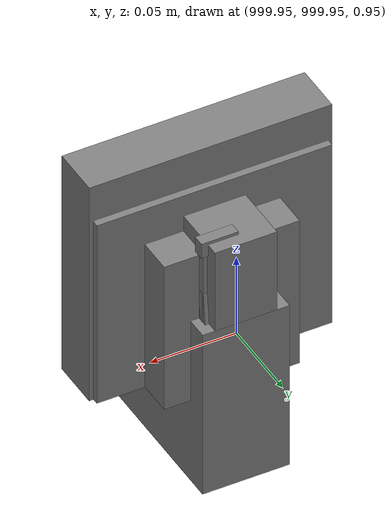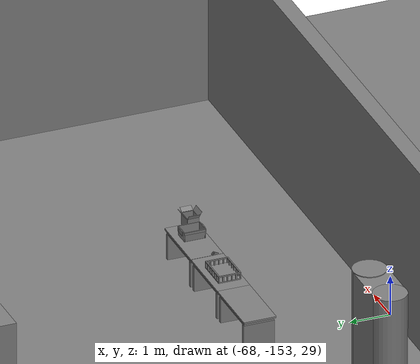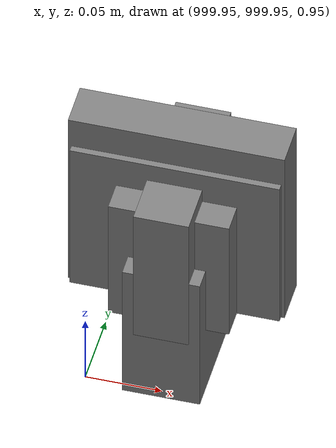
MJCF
<mujoco>
    <option gravity="0.000000000 0.000000000 -9.810000420" timestep="0.0049999999" integrator="implicitfast" density="1.225" viscosity="1.8000001e-05" noslip_iterations="10" iterations="100" sdf_iterations="50">
        <flag multiccd="disable"/>
    </option>
    <size memory="1000M"/>
    <compiler coordinate="local"/>
    <worldbody>
        <light cutoff="30" pos="0 1 1" dir="0 -1 -2"/>
        <light cutoff="30" pos="0 -1 1" dir="0 1 -2"/>
        <body pos="-64.866622925 -149.383972168 30.183746338" euler="89.999984741 89.999946594 0.000000000" name="openloong_gripper_2f85_fix_base_usda_bluebox_01">
            <geom contype="1" conaffinity="1" density="1000" type="box" material="" rgba="0.500000000 0.500000000 0.500000000 1.000000000" solimp="0.899999976 0.949999988 0.001000000" friction="1.000000000 0.005000000 0.000100000" solref="0.020000000 1.000000000" margin="0" condim="3" group="0" pos="0.276580811 0.187225342 0.000068665" quat="0.707106948 0.000077471 0.707106352 0.000077486" size="0.100000001 0.057999998 0.010000000" name="openloong_gripper_2f85_fix_base_usda_geom_0A62BD30_D042_467D_AF13_F883A597F27B"/>
            <geom contype="1" conaffinity="1" density="1000" type="box" material="" rgba="0.500000000 0.500000000 0.500000000 1.000000000" solimp="0.899999976 0.949999988 0.001000000" friction="1.000000000 0.005000000 0.000100000" solref="0.020000000 1.000000000" margin="0" condim="3" group="0" pos="0.000000000 0.002883911 0.000000000" quat="0.999999881 0.000000000 0.000000000 0.000000000" size="0.254000008 0.003000000 0.172000006" name="openloong_gripper_2f85_fix_base_usda_geom_53D7A94A_3267_47AF_B578_133719A5510B"/>
            <geom contype="1" conaffinity="1" density="1000" type="box" material="" rgba="0.500000000 0.500000000 0.500000000 1.000000000" solimp="0.899999976 0.949999988 0.001000000" friction="1.000000000 0.005000000 0.000100000" solref="0.020000000 1.000000000" margin="0" condim="3" group="0" pos="0.000000000 0.124874115 0.173484802" quat="0.999796331 0.020176515 -0.000000015 0.000000030" size="0.259999990 0.119999997 0.007000000" name="openloong_gripper_2f85_fix_base_usda_geom_4D86782A_1C54_41BB_B8D0_F95940AA324A"/>
            <geom contype="1" conaffinity="1" density="1000" type="box" material="" rgba="0.500000000 0.500000000 0.500000000 1.000000000" solimp="0.899999976 0.949999988 0.001000000" friction="1.000000000 0.005000000 0.000100000" solref="0.020000000 1.000000000" margin="0" condim="3" group="0" pos="0.000000000 0.124874115 -0.173469543" quat="0.999796331 -0.020176545 -0.000000015 0.000000000" size="0.259999990 0.119999997 0.007000000" name="openloong_gripper_2f85_fix_base_usda_geom_EFE165DA_6693_49CF_98E6_1986B2CB43B2"/>
            <geom contype="1" conaffinity="1" density="1000" type="box" material="" rgba="0.500000000 0.500000000 0.500000000 1.000000000" solimp="0.899999976 0.949999988 0.001000000" friction="1.000000000 0.005000000 0.000100000" solref="0.020000000 1.000000000" margin="0" condim="3" group="0" pos="0.000000000 0.214008331 0.188980103" quat="0.999912977 0.013176724 0.000000015 0.000000000" size="0.259999990 0.029999999 0.012500000" name="openloong_gripper_2f85_fix_base_usda_geom_588D98F7_E844_44AE_AD5A_1025827EE3E2"/>
            <geom contype="1" conaffinity="1" density="1000" type="box" material="" rgba="0.500000000 0.500000000 0.500000000 1.000000000" solimp="0.899999976 0.949999988 0.001000000" friction="1.000000000 0.005000000 0.000100000" solref="0.020000000 1.000000000" margin="0" condim="3" group="0" pos="-0.258361816 0.125289917 0.001876831" quat="0.702796936 -0.020792112 0.710783124 0.020769298" size="0.189999998 0.119999997 0.009000000" name="openloong_gripper_2f85_fix_base_usda_geom_194193E8_67EB_43A1_A6BF_78B5CEB144C5"/>
            <geom contype="1" conaffinity="1" density="1000" type="box" material="" rgba="0.500000000 0.500000000 0.500000000 1.000000000" solimp="0.899999976 0.949999988 0.001000000" friction="1.000000000 0.005000000 0.000100000" solref="0.020000000 1.000000000" margin="0" condim="3" group="0" pos="0.000000000 0.214008331 -0.188980103" quat="0.999912977 -0.013176769 0.000000030 0.000000015" size="0.259999990 0.029999999 0.012500000" name="openloong_gripper_2f85_fix_base_usda_geom_FEB37B2E_2C5D_4792_B73D_3EFB4B717A08"/>
            <geom contype="1" conaffinity="1" density="1000" type="box" material="" rgba="0.500000000 0.500000000 0.500000000 1.000000000" solimp="0.899999976 0.949999988 0.001000000" friction="1.000000000 0.005000000 0.000100000" solref="0.020000000 1.000000000" margin="0" condim="3" group="0" pos="-0.276611328 0.187225342 0.000068665" quat="0.707106650 0.000077441 0.707106709 0.000077456" size="0.100000001 0.057999998 0.010000000" name="openloong_gripper_2f85_fix_base_usda_geom_FD460AA2_88EE_497A_8ACB_4315D649C647"/>
            <geom contype="1" conaffinity="1" density="1000" type="box" material="" rgba="0.500000000 0.500000000 0.500000000 1.000000000" solimp="0.899999976 0.949999988 0.001000000" friction="1.000000000 0.005000000 0.000100000" solref="0.020000000 1.000000000" margin="0" condim="3" group="0" pos="0.258331299 0.125289917 0.001876831" quat="0.702851415 0.018856421 0.710823774 -0.019329369" size="0.189999998 0.119999997 0.009000000" name="openloong_gripper_2f85_fix_base_usda_geom_9DEBF9C3_5173_4E75_8124_EB5D48B8E8FE"/>
            <freejoint name="openloong_gripper_2f85_fix_base_usda_bluebox_01_joint"/>
            <site size="0.005000000 0.005000000 0.005000000" rgba="0.500000000 0.500000000 0.500000000 1.000000000" pos="0.000000000 0.000000000 0.000000000" quat="0.999961913 0.008726534 0.000000000 0.000000000" group="0" type="sphere" name="openloong_gripper_2f85_fix_base_usda_bluebox_01site"/>
        </body>
        <body pos="-64.496299744 -149.491867065 30.235729218" euler="0.000000000 0.000000000 89.999946594" name="openloong_gripper_2f85_fix_base_usda_cardboardbox_01">
            <geom contype="1" conaffinity="1" density="1000" type="box" material="" rgba="0.500000000 0.500000000 0.500000000 1.000000000" solimp="0.899999976 0.949999988 0.001000000" friction="1.000000000 0.005000000 0.000100000" solref="0.020000000 1.000000000" margin="0" condim="3" group="0" pos="-0.003166199 -0.004086494 0.005052090" quat="1.000000000 0.000000000 0.000000000 0.000000000" size="0.142499998 0.177500010 0.005000000" name="openloong_gripper_2f85_fix_base_usda_geom_E4C3B5C8_678A_4210_BC3F_427441087B19"/>
            <geom contype="1" conaffinity="1" density="1000" type="box" material="" rgba="0.500000000 0.500000000 0.500000000 1.000000000" solimp="0.899999976 0.949999988 0.001000000" friction="1.000000000 0.005000000 0.000100000" solref="0.020000000 1.000000000" margin="0" condim="3" group="0" pos="-0.003166199 0.170316696 0.150570869" quat="1.000000000 0.000000000 0.000000000 0.000000000" size="0.142499998 0.005000000 0.149999991" name="openloong_gripper_2f85_fix_base_usda_geom_425F1DBC_53E4_4B11_892E_88C604BB2086"/>
            <geom contype="1" conaffinity="1" density="1000" type="box" material="" rgba="0.500000000 0.500000000 0.500000000 1.000000000" solimp="0.899999976 0.949999988 0.001000000" friction="1.000000000 0.005000000 0.000100000" solref="0.020000000 1.000000000" margin="0" condim="3" group="0" pos="-0.147399902 -0.005307198 0.150570869" quat="1.000000000 0.000000000 0.000000000 0.000000000" size="0.005000000 0.177500010 0.149999991" name="openloong_gripper_2f85_fix_base_usda_geom_C737F9E2_8980_4D2B_A109_C2ADD405E42F"/>
            <geom contype="1" conaffinity="1" density="1000" type="box" material="" rgba="0.500000000 0.500000000 0.500000000 1.000000000" solimp="0.899999976 0.949999988 0.001000000" friction="1.000000000 0.005000000 0.000100000" solref="0.020000000 1.000000000" margin="0" condim="3" group="0" pos="0.140275955 -0.005307198 0.150570869" quat="1.000000000 0.000000000 0.000000000 0.000000000" size="0.005000000 0.177500010 0.149999991" name="openloong_gripper_2f85_fix_base_usda_geom_16BE8D35_85CC_438A_95D1_99A1C7E1A799"/>
            <geom contype="1" conaffinity="1" density="1000" type="box" material="" rgba="0.500000000 0.500000000 0.500000000 1.000000000" solimp="0.899999976 0.949999988 0.001000000" friction="1.000000000 0.005000000 0.000100000" solref="0.020000000 1.000000000" margin="0" condim="3" group="0" pos="-0.003166199 -0.181550980 0.150570869" quat="1.000000000 0.000000000 0.000000000 0.000000000" size="0.142499998 0.005000000 0.149999991" name="openloong_gripper_2f85_fix_base_usda_geom_2ACACCCB_E756_43D2_8374_614A03656111"/>
            <freejoint name="openloong_gripper_2f85_fix_base_usda_cardboardbox_01_joint"/>
            <site size="0.005000000 0.005000000 0.005000000" rgba="0.500000000 0.500000000 0.500000000 1.000000000" pos="0.000000000 0.000000000 0.000000000" quat="0.999961913 0.008726535 0.000000000 0.000000000" group="0" type="sphere" name="openloong_gripper_2f85_fix_base_usda_site_DDEA21E1_7C01_416C_AE8B_22251B82C655"/>
            <body pos="0.139160156 -0.004048347 0.301930904" euler="-179.999954224 49.383502960 179.999954224" name="openloong_gripper_2f85_fix_base_usda_A1_006">
                <geom contype="1" conaffinity="1" density="1000" type="box" material="" rgba="0.500000000 0.500000000 0.500000000 1.000000000" solimp="0.899999976 0.949999988 0.001000000" friction="1.000000000 0.005000000 0.000100000" solref="0.020000000 1.000000000" margin="0" condim="3" group="0" pos="-0.071587563 0.000009537 0.001745224" quat="0.999999881 0.000000000 0.000000000 0.000000000" size="0.071249999 0.179999992 0.002500000" name="openloong_gripper_2f85_fix_base_usda_geom_7764F927_4B5A_48F4_837E_FDFDC6B891CE"/>
                <joint armature="0" stiffness="0.07" damping="0.0099999998" axis="0.000000 1.000000 0.000000" type="hinge" name="openloong_gripper_2f85_fix_base_usda_A1_006"/>
            </body>
            <body pos="-0.145902634 -0.004086494 0.301938057" euler="-180.000000000 -60.000011444 -180.000000000" name="openloong_gripper_2f85_fix_base_usda_A2_006">
                <geom contype="1" conaffinity="1" density="1000" type="box" material="" rgba="0.500000000 0.500000000 0.500000000 1.000000000" solimp="0.899999976 0.949999988 0.001000000" friction="1.000000000 0.005000000 0.000100000" solref="0.020000000 1.000000000" margin="0" condim="3" group="0" pos="0.071268082 0.000009537 0.002717972" quat="0.000002921 0.000000000 -0.000000030 0.999999881" size="0.071249999 0.179999992 0.002500000" name="openloong_gripper_2f85_fix_base_usda_geom_BCBF95E7_39F4_4D44_9778_19E62FE63BF1"/>
                <joint armature="0" stiffness="0.07" damping="0.0099999998" axis="0.000000 1.000000 0.000000" type="hinge" name="openloong_gripper_2f85_fix_base_usda_A2_006"/>
            </body>
            <body pos="-0.003385544 0.175991058 0.301930904" euler="-125.858116150 -0.000004561 0.000002331" name="openloong_gripper_2f85_fix_base_usda_B2_006">
                <geom contype="1" conaffinity="1" density="1000" type="box" material="" rgba="0.500000000 0.500000000 0.500000000 1.000000000" solimp="0.899999976 0.949999988 0.001000000" friction="1.000000000 0.005000000 0.000100000" solref="0.020000000 1.000000000" margin="0" condim="3" group="0" pos="0.000009537 -0.070939064 -0.002470016" quat="0.999614120 0.027776197 -0.000000015 0.000000030" size="0.137500003 0.064999998 0.005000000" name="openloong_gripper_2f85_fix_base_usda_geom_3DA58183_021C_4B0C_BF44_5434CC30F1BF"/>
                <joint armature="0" stiffness="0.07" damping="0.0099999998" axis="1.000000 0.000000 0.000000" type="hinge" name="openloong_gripper_2f85_fix_base_usda_B2_006"/>
            </body>
            <body pos="-0.003385544 -0.184140205 0.301938057" euler="147.805557251 0.000000000 0.000000000" name="openloong_gripper_2f85_fix_base_usda_B1_006">
                <geom contype="1" conaffinity="1" density="1000" type="box" material="" rgba="0.500000000 0.500000000 0.500000000 1.000000000" solimp="0.899999976 0.949999988 0.001000000" friction="1.000000000 0.005000000 0.000100000" solref="0.020000000 1.000000000" margin="0" condim="3" group="0" pos="-0.000028610 0.070202351 -0.002703667" quat="0.999614179 -0.027776167 0.000000000 0.000000000" size="0.137500003 0.064999998 0.005000000" name="openloong_gripper_2f85_fix_base_usda_geom_6771BEBD_ABAB_4C59_BE57_BB27B689F556"/>
                <joint armature="0" stiffness="0.07" damping="0.0099999998" axis="1.000000 0.000000 0.000000" type="hinge" name="openloong_gripper_2f85_fix_base_usda_B1_006"/>
            </body>
        </body>
        <body pos="-65.882858276 -149.481979370 30.229999542" euler="-64.487716675 0.000000000 0.000000000" name="openloong_gripper_2f85_fix_base_usda_Barcode">
            <geom contype="1" conaffinity="1" density="1000" type="box" material="" rgba="0.500000000 0.500000000 0.500000000 1.000000000" solimp="0.899999976 0.949999988 0.001000000" friction="1.000000000 0.005000000 0.000100000" solref="0.020000000 1.000000000" margin="0" condim="3" group="0" pos="0.000000000 0.013038635 0.001419067" quat="0.000000000 0.000000000 0.000000000 1.000000119" size="0.034000002 0.010000000 0.017999999" name="openloong_gripper_2f85_fix_base_usda_geom_0B1881AC_37DF_4178_A787_9E48DCE0E4F8"/>
            <geom contype="1" conaffinity="1" density="1000" type="box" material="" rgba="0.500000000 0.500000000 0.500000000 1.000000000" solimp="0.899999976 0.949999988 0.001000000" friction="1.000000000 0.005000000 0.000100000" solref="0.020000000 1.000000000" margin="0" condim="3" group="0" pos="0.000000000 -0.035301208 -0.007095337" quat="0.000000000 0.000000000 -0.043619365 0.999048233" size="0.028999999 0.010000000 0.020000000" name="openloong_gripper_2f85_fix_base_usda_geom_7540658E_F256_466E_A668_DDC70C8DFF73"/>
            <geom contype="1" conaffinity="1" density="1000" type="box" material="" rgba="0.500000000 0.500000000 0.500000000 1.000000000" solimp="0.899999976 0.949999988 0.001000000" friction="1.000000000 0.005000000 0.000100000" solref="0.020000000 1.000000000" margin="0" condim="3" group="0" pos="0.000000000 -0.043411255 -0.011749268" quat="0.922262907 0.386563420 0.000000000 0.000000000" size="0.026000001 0.010000000 0.020000000" name="openloong_gripper_2f85_fix_base_usda_geom_AE063E15_162F_436E_A3F4_20CE0A8DD7F5"/>
            <geom contype="1" conaffinity="1" density="1000" type="box" material="" rgba="0.500000000 0.500000000 0.500000000 1.000000000" solimp="0.899999976 0.949999988 0.001000000" friction="1.000000000 0.005000000 0.000100000" solref="0.020000000 1.000000000" margin="0" condim="3" group="0" pos="0.000000000 -0.016967773 -0.031860352" quat="0.000000000 0.000000000 0.000000000 1.000000119" size="0.008000000 0.010000000 0.013000000" name="openloong_gripper_2f85_fix_base_usda_geom_68DE0963_4F2D_4B9E_A31E_FF35D4C2C3E6"/>
            <geom contype="1" conaffinity="1" density="1000" type="box" material="" rgba="0.500000000 0.500000000 0.500000000 1.000000000" solimp="0.899999976 0.949999988 0.001000000" friction="1.000000000 0.005000000 0.000100000" solref="0.020000000 1.000000000" margin="0" condim="3" group="0" pos="0.000000000 -0.001869202 0.000312805" quat="0.953716993 0.300705761 0.000000000 0.000000000" size="0.032000002 0.010000000 0.018999999" name="openloong_gripper_2f85_fix_base_usda_geom_F69BECF2_2CB5_49E0_BDAC_02C106755BB8"/>
            <geom contype="1" conaffinity="1" density="1000" type="box" material="" rgba="0.500000000 0.500000000 0.500000000 1.000000000" solimp="0.899999976 0.949999988 0.001000000" friction="1.000000000 0.005000000 0.000100000" solref="0.020000000 1.000000000" margin="0" condim="3" group="0" pos="0.000000000 -0.019531250 -0.003173828" quat="0.953716993 0.300705761 0.000000000 0.000000000" size="0.030999999 0.010000000 0.020000000" name="openloong_gripper_2f85_fix_base_usda_geom_1CEE6930_0296_4E13_8840_68DB1C507CA7"/>
            <geom contype="1" conaffinity="1" density="1000" type="box" material="" rgba="0.500000000 0.500000000 0.500000000 1.000000000" solimp="0.899999976 0.949999988 0.001000000" friction="1.000000000 0.005000000 0.000100000" solref="0.020000000 1.000000000" margin="0" condim="3" group="0" pos="0.000000000 -0.035301208 -0.007095337" quat="0.953716993 0.300705761 0.000000000 0.000000000" size="0.028999999 0.010000000 0.020000000" name="openloong_gripper_2f85_fix_base_usda_geom_FCD612E0_A03A_4892_86FA_E6EB460F87FC"/>
            <geom contype="1" conaffinity="1" density="1000" type="box" material="" rgba="0.500000000 0.500000000 0.500000000 1.000000000" solimp="0.899999976 0.949999988 0.001000000" friction="1.000000000 0.005000000 0.000100000" solref="0.020000000 1.000000000" margin="0" condim="3" group="0" pos="0.000000000 -0.042617798 -0.071121216" quat="0.000000000 0.000000000 0.000000000 1.000000119" size="0.013000000 0.021000000 0.059999999" name="openloong_gripper_2f85_fix_base_usda_geom_C32DC956_2036_4079_A37E_CEDDC441752D"/>
            <freejoint name="openloong_gripper_2f85_fix_base_usda_Barcode_joint"/>
            <site size="0.005000000 0.005000000 0.005000000" rgba="0.500000000 0.500000000 0.500000000 1.000000000" pos="0.000000000 0.000000000 0.000000000" quat="1.000000000 0.000000000 0.000000000 0.000000000" group="0" type="sphere" name="openloong_gripper_2f85_fix_base_usda_Barcode_site"/>
        </body>
        <body pos="-66.745018005 -149.392349243 30.184000015" euler="0.000000000 0.000000000 89.999946594" name="[22332808907290]_Basket_01">
            <geom contype="1" conaffinity="1" density="1000" type="box" material="" rgba="0.500000000 0.500000000 0.500000000 1.000000000" solimp="0.899999976 0.949999988 0.001000000" friction="1.000000000 0.005000000 0.000100000" solref="0.020000000 1.000000000" margin="0" condim="3" group="0" pos="-0.052425385 0.389207840 0.089787483" quat="0.707107008 0.000000000 0.000000000 0.707106411" size="0.014249999 0.014249999 0.059999999" name="[22332808907290]_geom_96A5E876_C82B_41EA_AD1F_985E2DBEC17D"/>
            <geom contype="1" conaffinity="1" density="1000" type="box" material="" rgba="0.500000000 0.500000000 0.500000000 1.000000000" solimp="0.899999976 0.949999988 0.001000000" friction="1.000000000 0.005000000 0.000100000" solref="0.020000000 1.000000000" margin="0" condim="3" group="0" pos="0.264015198 -0.133043289 0.089787483" quat="0.707107008 0.000000000 0.000000000 0.707106411" size="0.014249999 0.014249999 0.059999999" name="[22332808907290]_geom_7B79872B_3AE1_4A85_B4F5_001E74693E95"/>
            <geom contype="1" conaffinity="1" density="1000" type="box" material="" rgba="0.500000000 0.500000000 0.500000000 1.000000000" solimp="0.899999976 0.949999988 0.001000000" friction="1.000000000 0.005000000 0.000100000" solref="0.020000000 1.000000000" margin="0" condim="3" group="0" pos="-0.264015198 -0.265548706 0.089793205" quat="0.707107008 0.000000000 0.000000000 0.707106411" size="0.014249999 0.014249999 0.059999999" name="[22332808907290]_geom_093BA543_BEF4_4075_9F4A_67D7CBC5BBBE"/>
            <geom contype="1" conaffinity="1" density="1000" type="box" material="" rgba="0.500000000 0.500000000 0.500000000 1.000000000" solimp="0.899999976 0.949999988 0.001000000" friction="1.000000000 0.005000000 0.000100000" solref="0.020000000 1.000000000" margin="0" condim="3" group="0" pos="-0.160263062 -0.389322281 0.089793205" quat="0.707107008 0.000000000 0.000000000 0.707106411" size="0.014249999 0.014249999 0.059999999" name="[22332808907290]_geom_7493E32B_DAED_4C71_A89C_EEA49FC42885"/>
            <geom contype="1" conaffinity="1" density="1000" type="box" material="" rgba="0.500000000 0.500000000 0.500000000 1.000000000" solimp="0.899999976 0.949999988 0.001000000" friction="1.000000000 0.005000000 0.000100000" solref="0.020000000 1.000000000" margin="0" condim="3" group="0" pos="0.162265778 -0.389322281 0.089787483" quat="0.707107008 0.000000000 0.000000000 0.707106411" size="0.014249999 0.014249999 0.059999999" name="[22332808907290]_geom_523B0648_1DDF_4D7C_BB43_293F142FF2A5"/>
            <geom contype="1" conaffinity="1" density="1000" type="box" material="" rgba="0.500000000 0.500000000 0.500000000 1.000000000" solimp="0.899999976 0.949999988 0.001000000" friction="1.000000000 0.005000000 0.000100000" solref="0.020000000 1.000000000" margin="0" condim="3" group="0" pos="0.264015198 0.389207840 0.089787483" quat="0.707107008 0.000000000 0.000000000 0.707106411" size="0.014249999 0.014249999 0.059999999" name="[22332808907290]_geom_39AD5EA7_7CA3_488F_990F_B4509BEEE30C"/>
            <geom contype="1" conaffinity="1" density="1000" type="box" material="" rgba="0.500000000 0.500000000 0.500000000 1.000000000" solimp="0.899999976 0.949999988 0.001000000" friction="1.000000000 0.005000000 0.000100000" solref="0.020000000 1.000000000" margin="0" condim="3" group="0" pos="-0.264015198 -0.133043289 0.089793205" quat="0.707107008 0.000000000 0.000000000 0.707106411" size="0.014249999 0.014249999 0.059999999" name="[22332808907290]_geom_16ED1451_FC62_471B_B2E4_D859DCF54786"/>
            <geom contype="1" conaffinity="1" density="1000" type="box" material="" rgba="0.500000000 0.500000000 0.500000000 1.000000000" solimp="0.899999976 0.949999988 0.001000000" friction="1.000000000 0.005000000 0.000100000" solref="0.020000000 1.000000000" margin="0" condim="3" group="0" pos="-0.264026642 0.269256592 0.089793205" quat="0.707107008 0.000000000 0.000000000 0.707106411" size="0.014249999 0.014249999 0.059999999" name="[22332808907290]_geom_3B78CC38_D219_422D_8C43_8F1E4EBEDF63"/>
            <geom contype="1" conaffinity="1" density="1000" type="box" material="" rgba="0.500000000 0.500000000 0.500000000 1.000000000" solimp="0.899999976 0.949999988 0.001000000" friction="1.000000000 0.005000000 0.000100000" solref="0.020000000 1.000000000" margin="0" condim="3" group="0" pos="0.054462433 0.389207840 0.089787483" quat="0.707107008 0.000000000 0.000000000 0.707106411" size="0.014249999 0.014249999 0.059999999" name="[22332808907290]_geom_C7E67FE9_28EB_430E_9F8A_9F5AFC9A3857"/>
            <geom contype="1" conaffinity="1" density="1000" type="box" material="" rgba="0.500000000 0.500000000 0.500000000 1.000000000" solimp="0.899999976 0.949999988 0.001000000" friction="1.000000000 0.005000000 0.000100000" solref="0.020000000 1.000000000" margin="0" condim="3" group="0" pos="0.054462433 -0.389322281 0.089787483" quat="0.707107008 0.000000000 0.000000000 0.707106411" size="0.014249999 0.014249999 0.059999999" name="[22332808907290]_geom_5BECCB01_C9CA_4D19_A6C8_7CB0AAF82A25"/>
            <geom contype="1" conaffinity="1" density="1000" type="box" material="" rgba="0.500000000 0.500000000 0.500000000 1.000000000" solimp="0.899999976 0.949999988 0.001000000" friction="1.000000000 0.005000000 0.000100000" solref="0.020000000 1.000000000" margin="0" condim="3" group="0" pos="0.264015198 0.269256592 0.089793205" quat="0.707107008 0.000000000 0.000000000 0.707106411" size="0.014249999 0.014249999 0.059999999" name="[22332808907290]_geom_46E01A8D_D44E_4C4B_8562_E08205B31745"/>
            <geom contype="1" conaffinity="1" density="1000" type="box" material="" rgba="0.500000000 0.500000000 0.500000000 1.000000000" solimp="0.899999976 0.949999988 0.001000000" friction="1.000000000 0.005000000 0.000100000" solref="0.020000000 1.000000000" margin="0" condim="3" group="0" pos="0.264015198 -0.389322281 0.089787483" quat="0.707107008 0.000000000 0.000000000 0.707106411" size="0.014249999 0.014249999 0.059999999" name="[22332808907290]_geom_7E03E692_14B8_46B1_B15A_125B969D11B1"/>
            <geom contype="1" conaffinity="1" density="1000" type="box" material="" rgba="0.500000000 0.500000000 0.500000000 1.000000000" solimp="0.899999976 0.949999988 0.001000000" friction="1.000000000 0.005000000 0.000100000" solref="0.020000000 1.000000000" margin="0" condim="3" group="0" pos="0.000000000 0.000000000 0.015998840" quat="0.707107008 0.000000000 0.000000000 0.707106411" size="0.403499991 0.279000014 0.015750000" name="[22332808907290]_geom_D45CF6F7_2E06_4F62_B30E_00D7E5257F3C"/>
            <geom contype="1" conaffinity="1" density="1000" type="box" material="" rgba="0.500000000 0.500000000 0.500000000 1.000000000" solimp="0.899999976 0.949999988 0.001000000" friction="1.000000000 0.005000000 0.000100000" solref="0.020000000 1.000000000" margin="0" condim="3" group="0" pos="0.000000000 -0.389476776 0.163619041" quat="0.707107008 0.000000000 0.000000000 0.707106411" size="0.015000000 0.277500004 0.015750000" name="[22332808907290]_geom_82A9BF0A_165B_4093_A8B0_8E78F9FB36C1"/>
            <geom contype="1" conaffinity="1" density="1000" type="box" material="" rgba="0.500000000 0.500000000 0.500000000 1.000000000" solimp="0.899999976 0.949999988 0.001000000" friction="1.000000000 0.005000000 0.000100000" solref="0.020000000 1.000000000" margin="0" condim="3" group="0" pos="0.162265778 0.389207840 0.089787483" quat="0.707107008 0.000000000 0.000000000 0.707106411" size="0.014249999 0.014249999 0.059999999" name="[22332808907290]_geom_BC65ACF7_3B4B_477A_A7D9_F1B56D464811"/>
            <geom contype="1" conaffinity="1" density="1000" type="box" material="" rgba="0.500000000 0.500000000 0.500000000 1.000000000" solimp="0.899999976 0.949999988 0.001000000" friction="1.000000000 0.005000000 0.000100000" solref="0.020000000 1.000000000" margin="0" condim="3" group="0" pos="0.000000000 0.389471054 0.163619041" quat="0.707107008 0.000000000 0.000000000 0.707106411" size="0.015000000 0.277500004 0.015750000" name="[22332808907290]_geom_5A7C7E5E_ABD2_45C0_847B_BE057111BC4E"/>
            <geom contype="1" conaffinity="1" density="1000" type="box" material="" rgba="0.500000000 0.500000000 0.500000000 1.000000000" solimp="0.899999976 0.949999988 0.001000000" friction="1.000000000 0.005000000 0.000100000" solref="0.020000000 1.000000000" margin="0" condim="3" group="0" pos="-0.263511658 0.000000000 0.163619041" quat="0.707107008 0.000000000 0.000000000 0.707106411" size="0.403499991 0.015000000 0.015750000" name="[22332808907290]_geom_E00242FE_BA9E_4D76_80F3_7533F7544D74"/>
            <geom contype="1" conaffinity="1" density="1000" type="box" material="" rgba="0.500000000 0.500000000 0.500000000 1.000000000" solimp="0.899999976 0.949999988 0.001000000" friction="1.000000000 0.005000000 0.000100000" solref="0.020000000 1.000000000" margin="0" condim="3" group="0" pos="-0.264015198 0.141334534 0.089793205" quat="0.707107008 0.000000000 0.000000000 0.707106411" size="0.014249999 0.014249999 0.059999999" name="[22332808907290]_geom_C518E3C5_7E89_4B14_A3B0_56ED13BF1C42"/>
            <geom contype="1" conaffinity="1" density="1000" type="box" material="" rgba="0.500000000 0.500000000 0.500000000 1.000000000" solimp="0.899999976 0.949999988 0.001000000" friction="1.000000000 0.005000000 0.000100000" solref="0.020000000 1.000000000" margin="0" condim="3" group="0" pos="0.264015198 -0.265548706 0.089787483" quat="0.707107008 0.000000000 0.000000000 0.707106411" size="0.014249999 0.014249999 0.059999999" name="[22332808907290]_geom_AECB6605_F642_4ED5_826B_F6FD7976DC7B"/>
            <geom contype="1" conaffinity="1" density="1000" type="box" material="" rgba="0.500000000 0.500000000 0.500000000 1.000000000" solimp="0.899999976 0.949999988 0.001000000" friction="1.000000000 0.005000000 0.000100000" solref="0.020000000 1.000000000" margin="0" condim="3" group="0" pos="-0.160263062 0.389207840 0.089787483" quat="0.707107008 0.000000000 0.000000000 0.707106411" size="0.014249999 0.014249999 0.059999999" name="[22332808907290]_geom_F63BC06F_6BA4_4F95_8B7C_37E4F2E42375"/>
            <geom contype="1" conaffinity="1" density="1000" type="box" material="" rgba="0.500000000 0.500000000 0.500000000 1.000000000" solimp="0.899999976 0.949999988 0.001000000" friction="1.000000000 0.005000000 0.000100000" solref="0.020000000 1.000000000" margin="0" condim="3" group="0" pos="-0.052425385 -0.389322281 0.089787483" quat="0.707107008 0.000000000 0.000000000 0.707106411" size="0.014249999 0.014249999 0.059999999" name="[22332808907290]_geom_B94AA010_7566_4AFE_8A82_56425F8E6914"/>
            <geom contype="1" conaffinity="1" density="1000" type="box" material="" rgba="0.500000000 0.500000000 0.500000000 1.000000000" solimp="0.899999976 0.949999988 0.001000000" friction="1.000000000 0.005000000 0.000100000" solref="0.020000000 1.000000000" margin="0" condim="3" group="0" pos="-0.264026642 -0.389322281 0.089793205" quat="0.707107008 0.000000000 0.000000000 0.707106411" size="0.014249999 0.014249999 0.059999999" name="[22332808907290]_geom_30B1072E_B964_4F07_8669_249DEDFADD94"/>
            <geom contype="1" conaffinity="1" density="1000" type="box" material="" rgba="0.500000000 0.500000000 0.500000000 1.000000000" solimp="0.899999976 0.949999988 0.001000000" friction="1.000000000 0.005000000 0.000100000" solref="0.020000000 1.000000000" margin="0" condim="3" group="0" pos="0.264015198 0.141334534 0.089787483" quat="0.707107008 0.000000000 0.000000000 0.707106411" size="0.014249999 0.014249999 0.059999999" name="[22332808907290]_geom_0E0FC0D8_2CCA_4160_AC4F_6C2E120B5A0B"/>
            <geom contype="1" conaffinity="1" density="1000" type="box" material="" rgba="0.500000000 0.500000000 0.500000000 1.000000000" solimp="0.899999976 0.949999988 0.001000000" friction="1.000000000 0.005000000 0.000100000" solref="0.020000000 1.000000000" margin="0" condim="3" group="0" pos="-0.264015198 0.389207840 0.089793205" quat="0.707107008 0.000000000 0.000000000 0.707106411" size="0.014249999 0.014249999 0.059999999" name="[22332808907290]_geom_3203BD29_55DC_45CC_AED0_0A20828E2E6F"/>
            <geom contype="1" conaffinity="1" density="1000" type="box" material="" rgba="0.500000000 0.500000000 0.500000000 1.000000000" solimp="0.899999976 0.949999988 0.001000000" friction="1.000000000 0.005000000 0.000100000" solref="0.020000000 1.000000000" margin="0" condim="3" group="0" pos="0.264015198 0.004480362 0.089787483" quat="0.707107008 0.000000000 0.000000000 0.707106411" size="0.014249999 0.014249999 0.059999999" name="[22332808907290]_geom_326E9C63_541E_4E6F_8A1A_C1EFBE8E2662"/>
            <geom contype="1" conaffinity="1" density="1000" type="box" material="" rgba="0.500000000 0.500000000 0.500000000 1.000000000" solimp="0.899999976 0.949999988 0.001000000" friction="1.000000000 0.005000000 0.000100000" solref="0.020000000 1.000000000" margin="0" condim="3" group="0" pos="0.263694763 -0.000011444 0.163619041" quat="0.707107008 0.000000000 0.000000000 0.707106411" size="0.403499991 0.015000000 0.015750000" name="[22332808907290]_geom_0D479B5D_56C5_4160_BA1D_4ABCF2FE6D03"/>
            <geom contype="1" conaffinity="1" density="1000" type="box" material="" rgba="0.500000000 0.500000000 0.500000000 1.000000000" solimp="0.899999976 0.949999988 0.001000000" friction="1.000000000 0.005000000 0.000100000" solref="0.020000000 1.000000000" margin="0" condim="3" group="0" pos="-0.264015198 0.004480362 0.089793205" quat="0.707107008 0.000000000 0.000000000 0.707106411" size="0.014249999 0.014249999 0.059999999" name="[22332808907290]_geom_193811EA_B3ED_49C2_B30A_DB5E6D8D6DDB"/>
            <freejoint name="[22332808907290]_joint_75961EE7_4EA7_493C_B35A_23A8B436818E"/>
        </body>
        <body pos="0.000000000 0.000000000 0.000000000" euler="0.000000000 0.000000000 0.000000000" name="Static Objects_Static Objects">
            <geom contype="1" conaffinity="1" density="1000" type="box" material="" rgba="0.500000000 0.500000000 0.500000000 1.000000000" solimp="0.899999976 0.949999988 0.001000000" friction="1.000000000 0.005000000 0.000100000" solref="0.020000000 1.000000000" margin="0" condim="3" group="0" pos="-67.544113159 -149.365814209 29.727830887" quat="0.500000417 0.499999970 0.499999553 0.499999970" size="0.381000012 0.319999993 0.041000001" name="Static Objects_geom_0B0532B1_8B3A_4F99_9347_27D69D71B28E"/>
            <geom contype="1" conaffinity="1" density="1000" type="box" material="" rgba="0.500000000 0.500000000 0.500000000 1.000000000" solimp="0.899999976 0.949999988 0.001000000" friction="1.000000000 0.005000000 0.000100000" solref="0.020000000 1.000000000" margin="0" condim="3" group="0" pos="-68.239501953 -149.365814209 30.086868286" quat="0.500000417 0.499999970 0.499999553 0.499999970" size="0.370999992 0.039500002 0.745000005" name="Static Objects_geom_951D9194_8A52_4D32_BABE_6A21118CFDEC"/>
            <geom contype="1" conaffinity="1" density="1000" type="box" material="" rgba="0.500000000 0.500000000 0.500000000 1.000000000" solimp="0.899999976 0.949999988 0.001000000" friction="1.000000000 0.005000000 0.000100000" solref="0.020000000 1.000000000" margin="0" condim="3" group="0" pos="-68.239501953 -149.365814209 30.147235870" quat="0.500000417 0.499999970 0.499999553 0.499999970" size="0.400000006 0.022000000 0.800000012" name="Static Objects_geom_4CD0E4FC_55A5_4232_AABF_408714F5E602"/>
            <geom contype="1" conaffinity="1" density="1000" type="box" material="" rgba="0.500000000 0.500000000 0.500000000 1.000000000" solimp="0.899999976 0.949999988 0.001000000" friction="1.000000000 0.005000000 0.000100000" solref="0.020000000 1.000000000" margin="0" condim="3" group="0" pos="-68.934890747 -149.365814209 29.727830887" quat="0.500000417 0.499999970 0.499999553 0.499999970" size="0.381000012 0.319999993 0.041000001" name="Static Objects_geom_0AAABFC2_47E0_44FA_8E73_3FD2F8C1D6B8"/>
            <geom contype="1" conaffinity="1" density="1000" type="box" material="" rgba="0.500000000 0.500000000 0.500000000 1.000000000" solimp="0.899999976 0.949999988 0.001000000" friction="1.000000000 0.005000000 0.000100000" solref="0.020000000 1.000000000" margin="0" condim="3" group="0" pos="-68.239501953 -149.365814209 29.561563492" quat="0.500000417 0.499999970 0.499999553 0.499999970" size="0.020000000 0.022000000 0.660000026" name="Static Objects_geom_B3AD048A_95C5_455B_9D9B_13C9A90DD578"/>
            <geom contype="1" conaffinity="1" density="1000" type="box" material="" rgba="0.500000000 0.500000000 0.500000000 1.000000000" solimp="0.899999976 0.949999988 0.001000000" friction="1.000000000 0.005000000 0.000100000" solref="0.020000000 1.000000000" margin="0" condim="3" group="0" pos="-65.945671082 -149.365814209 29.727830887" quat="0.500000417 0.499999970 0.499999553 0.499999970" size="0.381000012 0.319999993 0.041000001" name="Static Objects_geom_1EC10144_59C3_47CF_A446_A4F8A75505D2"/>
            <geom contype="1" conaffinity="1" density="1000" type="box" material="" rgba="0.500000000 0.500000000 0.500000000 1.000000000" solimp="0.899999976 0.949999988 0.001000000" friction="1.000000000 0.005000000 0.000100000" solref="0.020000000 1.000000000" margin="0" condim="3" group="0" pos="-66.641059875 -149.365814209 30.086868286" quat="0.500000417 0.499999970 0.499999553 0.499999970" size="0.370999992 0.039500002 0.745000005" name="Static Objects_geom_C666CC87_D814_417C_9A87_75D1DCE70EC7"/>
            <geom contype="1" conaffinity="1" density="1000" type="box" material="" rgba="0.500000000 0.500000000 0.500000000 1.000000000" solimp="0.899999976 0.949999988 0.001000000" friction="1.000000000 0.005000000 0.000100000" solref="0.020000000 1.000000000" margin="0" condim="3" group="0" pos="-66.641059875 -149.365814209 30.147235870" quat="0.500000417 0.499999970 0.499999553 0.499999970" size="0.400000006 0.022000000 0.800000012" name="Static Objects_geom_F10ECC61_4301_4F6F_9CEE_E76AAB5BB5A3"/>
            <geom contype="1" conaffinity="1" density="1000" type="box" material="" rgba="0.500000000 0.500000000 0.500000000 1.000000000" solimp="0.899999976 0.949999988 0.001000000" friction="1.000000000 0.005000000 0.000100000" solref="0.020000000 1.000000000" margin="0" condim="3" group="0" pos="-67.336448669 -149.365814209 29.727830887" quat="0.500000417 0.499999970 0.499999553 0.499999970" size="0.381000012 0.319999993 0.041000001" name="Static Objects_geom_9DAD208A_2EF0_4708_AE50_071F2196243A"/>
            <geom contype="1" conaffinity="1" density="1000" type="box" material="" rgba="0.500000000 0.500000000 0.500000000 1.000000000" solimp="0.899999976 0.949999988 0.001000000" friction="1.000000000 0.005000000 0.000100000" solref="0.020000000 1.000000000" margin="0" condim="3" group="0" pos="-66.641059875 -149.365814209 29.561563492" quat="0.500000417 0.499999970 0.499999553 0.499999970" size="0.020000000 0.022000000 0.660000026" name="Static Objects_geom_5FFA1D12_0D61_423F_B6C7_F5D006ADE35D"/>
            <geom contype="1" conaffinity="1" density="1000" type="box" material="" rgba="0.500000000 0.500000000 0.500000000 1.000000000" solimp="0.899999976 0.949999988 0.001000000" friction="1.000000000 0.005000000 0.000100000" solref="0.020000000 1.000000000" margin="0" condim="3" group="0" pos="-64.338577271 -149.365814209 29.727830887" quat="0.500000417 0.499999970 0.499999553 0.499999970" size="0.381000012 0.319999993 0.041000001" name="Static Objects_geom_5402201C_B9A3_4F52_AC1A_FDDA1FF7E0EE"/>
            <geom contype="1" conaffinity="1" density="1000" type="box" material="" rgba="0.500000000 0.500000000 0.500000000 1.000000000" solimp="0.899999976 0.949999988 0.001000000" friction="1.000000000 0.005000000 0.000100000" solref="0.020000000 1.000000000" margin="0" condim="3" group="0" pos="-65.033966064 -149.365814209 30.086868286" quat="0.500000417 0.499999970 0.499999553 0.499999970" size="0.370999992 0.039500002 0.745000005" name="Static Objects_geom_5F79EBE8_52CC_4579_A484_19A0BDC1F081"/>
            <geom contype="1" conaffinity="1" density="1000" type="box" material="" rgba="0.500000000 0.500000000 0.500000000 1.000000000" solimp="0.899999976 0.949999988 0.001000000" friction="1.000000000 0.005000000 0.000100000" solref="0.020000000 1.000000000" margin="0" condim="3" group="0" pos="-65.033966064 -149.365814209 30.147235870" quat="0.500000417 0.499999970 0.499999553 0.499999970" size="0.400000006 0.022000000 0.800000012" name="Static Objects_geom_DC783D64_7627_4A1E_BD95_1584EF322593"/>
            <geom contype="1" conaffinity="1" density="1000" type="box" material="" rgba="0.500000000 0.500000000 0.500000000 1.000000000" solimp="0.899999976 0.949999988 0.001000000" friction="1.000000000 0.005000000 0.000100000" solref="0.020000000 1.000000000" margin="0" condim="3" group="0" pos="-65.729354858 -149.365814209 29.727830887" quat="0.500000417 0.499999970 0.499999553 0.499999970" size="0.381000012 0.319999993 0.041000001" name="Static Objects_geom_B5CA9CDD_1765_4A28_B8D5_F82AB3D3A1D7"/>
            <geom contype="1" conaffinity="1" density="1000" type="box" material="" rgba="0.500000000 0.500000000 0.500000000 1.000000000" solimp="0.899999976 0.949999988 0.001000000" friction="1.000000000 0.005000000 0.000100000" solref="0.020000000 1.000000000" margin="0" condim="3" group="0" pos="-65.033966064 -149.365814209 29.561563492" quat="0.500000417 0.499999970 0.499999553 0.499999970" size="0.020000000 0.022000000 0.660000026" name="Static Objects_geom_98250516_BE6D_4A7A_B202_F85F0B7438C4"/>
            <geom contype="1" conaffinity="1" density="1000" type="box" material="" rgba="0.500000000 0.500000000 0.500000000 1.000000000" solimp="0.899999976 0.949999988 0.001000000" friction="1.000000000 0.005000000 0.000100000" solref="0.020000000 1.000000000" margin="0" condim="3" group="0" pos="-61.754566193 -137.853729248 33.906845093" quat="0.707107067 0.000000000 0.000000000 0.707106471" size="0.759999990 0.759999990 4.500000000" name="Static Objects_geom_E8354FF4_3D4F_4FF6_B1D5_2C539470D3F1"/>
            <geom contype="1" conaffinity="1" density="1000" type="box" material="" rgba="0.500000000 0.500000000 0.500000000 1.000000000" solimp="0.899999976 0.949999988 0.001000000" friction="1.000000000 0.005000000 0.000100000" solref="0.020000000 1.000000000" margin="0" condim="3" group="0" pos="-57.511135101 -144.927108765 31.707921982" quat="1.000000000 0.000000000 0.000000000 0.000000000" size="0.200000003 8.000000000 2.299999952" name="Static Objects_geom_F14CD456_F5D0_45F8_8602_E3264B172AEA"/>
            <geom contype="1" conaffinity="1" density="1000" type="box" material="" rgba="0.500000000 0.500000000 0.500000000 1.000000000" solimp="0.899999976 0.949999988 0.001000000" friction="1.000000000 0.005000000 0.000100000" solref="0.020000000 1.000000000" margin="0" condim="3" group="0" pos="-80.517646790 -157.574050903 31.688196182" quat="0.707107067 0.000000000 0.000000000 0.707106471" size="0.600000024 0.600000024 2.299999952" name="Static Objects_geom_3D598C5F_0F63_40D5_9A98_05E69D6CA3DF"/>
            <geom contype="1" conaffinity="1" density="1000" type="box" material="" rgba="0.500000000 0.500000000 0.500000000 1.000000000" solimp="0.899999976 0.949999988 0.001000000" friction="1.000000000 0.005000000 0.000100000" solref="0.020000000 1.000000000" margin="0" condim="3" group="0" pos="-80.711044312 -147.414932251 31.666158676" quat="1.000000000 0.000000000 0.000000000 0.000000000" size="0.200000003 10.000000000 2.299999952" name="Static Objects_geom_24D55C8C_9F68_4170_92B8_EE74B867E3EE"/>
            <geom contype="1" conaffinity="1" density="1000" type="box" material="" rgba="0.500000000 0.500000000 0.500000000 1.000000000" solimp="0.899999976 0.949999988 0.001000000" friction="1.000000000 0.005000000 0.000100000" solref="0.020000000 1.000000000" margin="0" condim="3" group="0" pos="-57.687217712 -137.434692383 31.688196182" quat="0.707107067 0.000000000 0.000000000 0.707106471" size="0.600000024 0.600000024 2.299999952" name="Static Objects_geom_116E8D60_A0B9_4BEB_9535_F1CD7A0BD9B3"/>
            <geom contype="1" conaffinity="1" density="1000" type="box" material="" rgba="0.500000000 0.500000000 0.500000000 1.000000000" solimp="0.899999976 0.949999988 0.001000000" friction="1.000000000 0.005000000 0.000100000" solref="0.020000000 1.000000000" margin="0" condim="3" group="0" pos="-69.537033081 -140.263229370 31.714921951" quat="0.707107067 0.000000000 0.000000000 0.707106471" size="0.759999990 4.500000000 2.299999952" name="Static Objects_geom_3371EC99_F74B_443B_AF88_5DF58ED3B7F1"/>
            <geom contype="1" conaffinity="1" density="1000" type="box" material="" rgba="0.500000000 0.500000000 0.500000000 1.000000000" solimp="0.899999976 0.949999988 0.001000000" friction="1.000000000 0.005000000 0.000100000" solref="0.020000000 1.000000000" margin="0" condim="3" group="0" pos="-80.073638916 -137.853713989 33.906845093" quat="0.707107067 0.000000000 0.000000000 0.707106471" size="0.759999990 0.759999990 4.500000000" name="Static Objects_geom_30E8570B_F8D6_4622_89A2_84E282E1DCC6"/>
            <geom contype="1" conaffinity="1" density="1000" type="box" material="" rgba="0.500000000 0.500000000 0.500000000 1.000000000" solimp="0.899999976 0.949999988 0.001000000" friction="1.000000000 0.005000000 0.000100000" solref="0.020000000 1.000000000" margin="0" condim="3" group="0" pos="-73.406707764 -155.734664917 31.707921982" quat="1.000000000 0.000000000 0.000000000 0.000000000" size="0.200000003 3.000000000 2.299999952" name="Static Objects_geom_F9B79A59_B495_406C_B1E9_CB4549E9DDCC"/>
            <geom contype="1" conaffinity="1" density="1000" type="box" material="" rgba="0.500000000 0.500000000 0.500000000 1.000000000" solimp="0.899999976 0.949999988 0.001000000" friction="1.000000000 0.005000000 0.000100000" solref="0.020000000 1.000000000" margin="0" condim="3" group="0" pos="-68.497543335 -137.448257446 31.707921982" quat="0.707107067 0.000000000 0.000000000 0.707106471" size="0.200000003 14.000000000 2.299999952" name="Static Objects_geom_75BC90DC_3D02_46F0_AAFB_1B62C35AF102"/>
            <geom contype="1" conaffinity="1" density="1000" type="cylinder" material="" rgba="0.500000000 0.500000000 0.500000000 1.000000000" solimp="0.899999976 0.949999988 0.001000000" friction="1.000000000 0.005000000 0.000100000" solref="0.020000000 1.000000000" margin="0" condim="3" group="0" pos="-68.868522644 -142.134506226 31.711090088" quat="0.707107067 0.000000000 0.000000000 0.707106471" size="0.509999990 2.299999952 1.000000000" name="Static Objects_geom_35888074_88DA_49DE_AB97_3078F278B74E"/>
            <geom contype="1" conaffinity="1" density="1000" type="plane" material="" rgba="0.500000000 0.500000000 0.500000000 1.000000000" solimp="0.899999976 0.949999988 0.001000000" friction="1.000000000 0.005000000 0.000100000" solref="0.020000000 1.000000000" margin="0" condim="3" group="0" pos="-72.873703003 -147.131927490 29.409669876" quat="1.000000000 0.000000000 0.000000000 0.000000000" size="18.000000000 14.000000000 1.000000000" name="Static Objects_geom_E8C0B1FB_14E4_485D_B99C_FC81ACFE129E"/>
            <geom contype="1" conaffinity="1" density="1000" type="box" material="" rgba="0.500000000 0.500000000 0.500000000 1.000000000" solimp="0.899999976 0.949999988 0.001000000" friction="1.000000000 0.005000000 0.000100000" solref="0.020000000 1.000000000" margin="0" condim="3" group="0" pos="-79.943580627 -157.782272339 31.707921982" quat="0.707107067 0.000000000 0.000000000 0.707106471" size="0.200000003 7.000000000 2.299999952" name="Static Objects_geom_B1DDD698_784D_4635_A152_845A59BDF564"/>
            <geom contype="1" conaffinity="1" density="1000" type="box" material="" rgba="0.500000000 0.500000000 0.500000000 1.000000000" solimp="0.899999976 0.949999988 0.001000000" friction="1.000000000 0.005000000 0.000100000" solref="0.020000000 1.000000000" margin="0" condim="3" group="0" pos="-65.421028137 -152.903442383 31.707921982" quat="0.707107067 0.000000000 0.000000000 0.707106471" size="0.200000003 7.800000191 2.299999952" name="Static Objects_geom_3020252F_5099_4441_8FB1_BB9B0F4C32FE"/>
            <geom contype="1" conaffinity="1" density="1000" type="box" material="" rgba="0.500000000 0.500000000 0.500000000 1.000000000" solimp="0.899999976 0.949999988 0.001000000" friction="1.000000000 0.005000000 0.000100000" solref="0.020000000 1.000000000" margin="0" condim="3" group="0" pos="-74.776908875 -149.964416504 31.688196182" quat="1.000000000 0.000000000 0.000000000 0.000000000" size="0.600000024 0.409999996 2.299999952" name="Static Objects_geom_8C92035B_8483_4FD9_96E9_3E769A3CC44A"/>
            <geom contype="1" conaffinity="1" density="1000" type="cylinder" material="" rgba="0.500000000 0.500000000 0.500000000 1.000000000" solimp="0.899999976 0.949999988 0.001000000" friction="1.000000000 0.005000000 0.000100000" solref="0.020000000 1.000000000" margin="0" condim="3" group="0" pos="-60.161884308 -142.134506226 31.711090088" quat="0.707107067 0.000000000 0.000000000 0.707106471" size="0.509999990 2.299999952 1.000000000" name="Static Objects_geom_4734245F_1153_4B3A_AF24_CEA3CF7F5BEA"/>
            <geom contype="1" conaffinity="1" density="1000" type="cylinder" material="" rgba="0.500000000 0.500000000 0.500000000 1.000000000" solimp="0.899999976 0.949999988 0.001000000" friction="1.000000000 0.005000000 0.000100000" solref="0.020000000 1.000000000" margin="0" condim="3" group="0" pos="-75.382453918 -149.963455200 31.711090088" quat="0.707107067 0.000000000 0.000000000 0.707106471" size="0.409999996 2.299999952 1.000000000" name="Static Objects_geom_AB8018CD_E1BE_49B5_8278_3519B2A7C66B"/>
            <geom contype="1" conaffinity="1" density="1000" type="cylinder" material="" rgba="0.500000000 0.500000000 0.500000000 1.000000000" solimp="0.899999976 0.949999988 0.001000000" friction="1.000000000 0.005000000 0.000100000" solref="0.020000000 1.000000000" margin="0" condim="3" group="0" pos="-74.154960632 -149.963455200 31.711090088" quat="0.707107067 0.000000000 0.000000000 0.707106471" size="0.409999996 2.299999952 1.000000000" name="Static Objects_geom_5DE8B85D_7340_4876_87F3_1FF100BA2D27"/>
            <geom contype="1" conaffinity="1" density="1000" type="cylinder" material="" rgba="0.500000000 0.500000000 0.500000000 1.000000000" solimp="0.899999976 0.949999988 0.001000000" friction="1.000000000 0.005000000 0.000100000" solref="0.020000000 1.000000000" margin="0" condim="3" group="0" pos="-77.566612244 -142.134506226 31.711090088" quat="0.707107067 0.000000000 0.000000000 0.707106471" size="0.509999990 2.299999952 1.000000000" name="Static Objects_geom_F9024E84_052F_4CD0_A731_91E6F2EE9E9A"/>
        </body>
        <body pos="1000.000000000 1000.000000000 1.000000000" euler="0.000000000 0.000000000 180.000000000" name="openloong_gripper_2f85_fix_base_usda_cpu_fan">
            <geom contype="1" conaffinity="1" density="1000" type="box" material="" rgba="0.500000000 0.500000000 0.500000000 1.000000000" solimp="0.899999976 0.949999988 0.001000000" friction="1.000000000 0.005000000 0.000100000" solref="0.020000000 1.000000000" margin="0" condim="3" group="0" pos="0.000000000 0.000000000 0.070034981" quat="0.000000000 0.000000000 0.000000000 1.000000000" size="0.070700005 0.014699999 0.070700005" name="openloong_gripper_2f85_fix_base_usda_geom_74BC11C5_C133_4441_B54C_FFC0E52879C1"/>
            <freejoint name="openloong_gripper_2f85_fix_base_usda_cpu_fan_joint"/>
            <site size="0.005000000 0.005000000 0.005000000" rgba="0.500000000 0.500000000 0.500000000 1.000000000" pos="0.000000000 0.000000000 0.000000000" quat="0.999961913 0.008726535 0.000000000 0.000000000" group="0" type="sphere" name="openloong_gripper_2f85_fix_base_usda_cpu_fancsite"/>
        </body>
        <body pos="1000.000000000 1000.000000000 1.000000000" euler="0.000000000 0.000000000 180.000000000" name="openloong_gripper_2f85_fix_base_usda_battery_01">
            <geom contype="1" conaffinity="1" density="1000" type="box" material="" rgba="0.500000000 0.500000000 0.500000000 1.000000000" solimp="0.899999976 0.949999988 0.001000000" friction="1.000000000 0.005000000 0.000100000" solref="0.020000000 1.000000000" margin="0" condim="3" group="0" pos="-0.011123657 -0.041940309 0.101691343" quat="1.000000000 0.000000000 0.000000000 0.000000000" size="0.010800000 0.003375000 0.004725000" name="openloong_gripper_2f85_fix_base_usda_geom_1C828C24_D259_40EB_97FA_9BC224FEBF1F"/>
            <geom contype="1" conaffinity="1" density="1000" type="box" material="" rgba="0.500000000 0.500000000 0.500000000 1.000000000" solimp="0.899999976 0.949999988 0.001000000" friction="1.000000000 0.005000000 0.000100000" solref="0.020000000 1.000000000" margin="0" condim="3" group="0" pos="-0.010876465 -0.044247437 0.047066893" quat="0.998702705 -0.050920475 0.000000000 0.000000000" size="0.009450001 0.002700000 0.024975000" name="openloong_gripper_2f85_fix_base_usda_geom_25A3B62E_6529_4524_9990_8D2B216B0933"/>
            <geom contype="1" conaffinity="1" density="1000" type="box" material="" rgba="0.500000000 0.500000000 0.500000000 1.000000000" solimp="0.899999976 0.949999988 0.001000000" friction="1.000000000 0.005000000 0.000100000" solref="0.020000000 1.000000000" margin="0" condim="3" group="0" pos="-0.001235962 -0.000659180 0.047381196" quat="1.000000000 0.000000000 0.000000000 0.000000000" size="0.039420001 0.039150000 0.047250003" name="openloong_gripper_2f85_fix_base_usda_geom_4DFD0CE0_1F1E_4FB2_93EF_8A21EEF4D4C6"/>
            <geom contype="1" conaffinity="1" density="1000" type="box" material="" rgba="0.500000000 0.500000000 0.500000000 1.000000000" solimp="0.899999976 0.949999988 0.001000000" friction="1.000000000 0.005000000 0.000100000" solref="0.020000000 1.000000000" margin="0" condim="3" group="0" pos="-0.010876465 -0.039138794 0.009851727" quat="1.000000000 0.000000000 0.000000000 0.000000000" size="0.009450001 0.010800000 0.013500000" name="openloong_gripper_2f85_fix_base_usda_geom_594EFDAB_5ACC_4289_B260_A0F41E19D864"/>
            <geom contype="1" conaffinity="1" density="1000" type="box" material="" rgba="0.500000000 0.500000000 0.500000000 1.000000000" solimp="0.899999976 0.949999988 0.001000000" friction="1.000000000 0.005000000 0.000100000" solref="0.020000000 1.000000000" margin="0" condim="3" group="0" pos="-0.010876465 -0.041528322 0.071508206" quat="1.000000000 0.000000000 0.000000000 0.000000000" size="0.009450001 0.002700000 0.027000001" name="openloong_gripper_2f85_fix_base_usda_geom_BA296708_A10B_4CAA_A558_87A0D9F7C7DD"/>
            <freejoint name="openloong_gripper_2f85_fix_base_usda_battery_01_joint"/>
            <site size="0.005000000 0.005000000 0.005000000" rgba="0.500000000 0.500000000 0.500000000 1.000000000" pos="0.000000000 0.000000000 0.000000000" quat="0.999961913 0.008726500 0.000000000 0.000000000" group="0" type="sphere" name="openloong_gripper_2f85_fix_base_usda_battery_01site"/>
        </body>
        <body pos="1000.000000000 1000.000000000 1.000000000" euler="0.000000000 0.000000000 180.000000000" name="openloong_gripper_2f85_fix_base_usda_wifi_box">
            <geom contype="1" conaffinity="1" density="1000" type="box" material="" rgba="0.500000000 0.500000000 0.500000000 1.000000000" solimp="0.899999976 0.949999988 0.001000000" friction="1.000000000 0.005000000 0.000100000" solref="0.020000000 1.000000000" margin="0" condim="3" group="0" pos="0.000000000 0.000000000 0.058978677" quat="0.000000000 0.000000047 0.000000000 1.000000000" size="0.068499997 0.018999999 0.059000000" name="openloong_gripper_2f85_fix_base_usda_geom_A63CBD9A_2E2A_47DD_B333_49104454FD81"/>
            <freejoint name="openloong_gripper_2f85_fix_base_usda_wifi_box_joint"/>
            <site size="0.005000000 0.005000000 0.005000000" rgba="0.500000000 0.500000000 0.500000000 1.000000000" pos="0.000000000 0.000000000 0.000000000" quat="0.999961913 0.008726500 0.000000000 0.000000000" group="0" type="sphere" name="openloong_gripper_2f85_fix_base_usda_wifi_boxsite"/>
        </body>
        <body pos="-66.107170105 -149.511367798 31.170984268" euler="-126.223556519 -33.640846252 -87.547882080" mocap="true" name="spotlight6_SpotLight"/>
        <body pos="-66.393905640 -149.564056396 31.165578842" euler="-83.922576904 -5.579999924 29.189468384" mocap="true" name="spotlight1_SpotLight"/>
        <body pos="1000.000000000 999.999938965 1.000000000" euler="0.000000000 0.000000000 180.000000000" name="openloong_gripper_2f85_fix_base_usda_intelcore_i5">
            <geom contype="1" conaffinity="1" density="1000" type="box" material="" rgba="0.500000000 0.500000000 0.500000000 1.000000000" solimp="0.899999976 0.949999988 0.001000000" friction="1.000000000 0.005000000 0.000100000" solref="0.020000000 1.000000000" margin="0" condim="3" group="0" pos="0.000000000 0.000000000 0.051722717" quat="0.707106709 0.000000000 0.000000000 -0.707106769" size="0.052800000 0.018080002 0.052800000" name="openloong_gripper_2f85_fix_base_usda_geom_D999728D_589A_4EF0_A7E6_21A214ECFB04"/>
            <freejoint name="openloong_gripper_2f85_fix_base_usda_intelcore_i5_joint"/>
            <site size="0.005000000 0.005000000 0.005000000" rgba="0.500000000 0.500000000 0.500000000 1.000000000" pos="0.000000000 0.000000000 0.000000000" quat="0.999961913 0.008726534 0.000000000 0.000000000" group="0" type="sphere" name="openloong_gripper_2f85_fix_base_usda_intelcore_i5site"/>
        </body>
        <body pos="1000.000000000 1000.000000000 1.000000000" euler="0.000011953 0.000005123 -179.999984741" name="openloong_gripper_2f85_fix_base_usda_intel_box">
            <geom contype="1" conaffinity="1" density="1000" type="box" material="" rgba="0.500000000 0.500000000 0.500000000 1.000000000" solimp="0.899999976 0.949999988 0.001000000" friction="1.000000000 0.005000000 0.000100000" solref="0.020000000 1.000000000" margin="0" condim="3" group="0" pos="0.000000000 -0.000067139 0.000082284" quat="0.707106709 0.000000225 0.000000253 0.707106650" size="0.052800003 0.025300000 0.052800003" name="openloong_gripper_2f85_fix_base_usda_geom_68BA2249_1334_4A10_BBD8_DE6A917AFF65"/>
            <freejoint name="openloong_gripper_2f85_fix_base_usda_intel_box_joint"/>
            <site size="0.005000000 0.005000000 0.005000000" rgba="0.500000000 0.500000000 0.500000000 1.000000000" pos="0.000000000 0.000000000 0.000000000" quat="0.999961913 0.008726500 0.000000000 0.000000000" group="0" type="sphere" name="openloong_gripper_2f85_fix_base_usda_intel_boxsite"/>
        </body>
        <body pos="-66.186492920 -149.093276978 31.165224075" euler="-114.881889343 -17.468835831 -17.370639801" mocap="true" name="spotlight4_SpotLight"/>
        <body pos="-66.291030884 -149.869689941 29.018842697" euler="0.000000000 0.000000000 89.999946594" mocap="true" name="openloong_gripper_2f85_fix_base_usda_leftHandMocap"/>
        <body pos="-66.291030884 -149.869689941 29.018842697" euler="0.000000000 0.000000000 89.999946594" mocap="true" name="openloong_gripper_2f85_fix_base_usda_rightHandMocap"/>
        <body pos="-66.291030884 -149.869689941 30.218843460" euler="0.000000000 0.000000000 89.999946594" name="openloong_gripper_2f85_fix_base_usda_base_link">
            <geom contype="1" conaffinity="1" density="1000" type="mesh" material="" rgba="0.783999979 0.783999979 0.783999979 1.000000000" solimp="0.899999976 0.949999988 0.001000000" friction="1.000000000 0.005000000 0.000100000" solref="0.020000000 1.000000000" margin="0" condim="3" group="3" mesh="base_link" pos="0.000000000 0.000000000 0.000000000" quat="1.000000000 0.000000000 0.000000000 0.000000000" size="1.000000000 1.000000000 1.000000000" name="openloong_gripper_2f85_fix_base_usda__geom_7_57A3621C_DA77_447A_8D02_6C109A04C392"/>
            <site size="0.005000000 0.005000000 0.005000000" rgba="0.500000000 0.500000000 0.500000000 1.000000000" pos="0.000000000 0.000000000 0.000000000" quat="1.000000000 0.000000000 0.000000000 0.000000000" group="0" type="sphere" name="openloong_gripper_2f85_fix_base_usda_imu"/>
            <inertial mass="22.447001" pos="-0.005664100 -0.001336700 0.238289997" diaginertia="0.374352545 0.277180195 0.220617250" quat="0.999247074 0.035235517 -0.015086859 0.006023135"/>
            <body pos="0.000000000 0.000000000 0.299997330" euler="0.000000000 0.000000000 0.000000000" name="openloong_gripper_2f85_fix_base_usda_dummy_body">
                <geom contype="1" conaffinity="1" density="1000" type="sphere" material="" rgba="0.783999979 0.783999979 0.783999979 1.000000000" solimp="0.899999976 0.949999988 0.001000000" friction="1.000000000 0.005000000 0.000100000" solref="0.020000000 1.000000000" margin="0" condim="3" group="3" pos="0.000000000 0.000000000 0.000000000" quat="1.000000000 0.000000000 0.000000000 0.000000000" size="0.010000000 0.000000000 0.000000000" name="openloong_gripper_2f85_fix_base_usda__geom_8_55F7EE79_0B05_4C77_81E2_EBA3EF519186"/>
                <joint armature="0.0099999998" stiffness="0" damping="0.1" axis="0.000000 0.000000 1.000000" type="hinge" name="openloong_gripper_2f85_fix_base_usda_dummy_joint"/>
                <site size="0.010000000 0.005000000 0.005000000" rgba="0.500000000 0.500000000 0.500000000 1.000000000" pos="0.000000000 0.000000000 0.000000000" quat="1.000000000 0.000000000 0.000000000 0.000000000" group="3" type="sphere" name="openloong_gripper_2f85_fix_base_usda_dummy_site"/>
            </body>
            <body pos="0.009002686 0.000000000 0.406400681" euler="0.000000000 0.000000000 0.000000000" name="openloong_gripper_2f85_fix_base_usda_Link_head_yaw">
                <geom contype="1" conaffinity="1" density="1000" type="mesh" material="" rgba="0.783999979 0.783999979 0.783999979 1.000000000" solimp="0.899999976 0.949999988 0.001000000" friction="1.000000000 0.005000000 0.000100000" solref="0.020000000 1.000000000" margin="0" condim="3" group="3" mesh="Link_head_yaw" pos="0.000000000 0.000000000 0.000000000" quat="1.000000000 0.000000000 0.000000000 0.000000000" size="1.000000000 1.000000000 1.000000000" name="openloong_gripper_2f85_fix_base_usda__geom_10_BDA190E9_18E1_4158_A72C_582D03B829AE"/>
                <inertial mass="0.84249002" pos="0.000000000 -0.002081400 0.044801001" diaginertia="0.000700588 0.000629000 0.000553812" quat="0.706933022 -0.015675601 0.015677100 0.706933022"/>
                <body pos="0.000000000 -0.034599304 0.048500061" euler="0.000000000 0.000000000 0.000000000" name="openloong_gripper_2f85_fix_base_usda_Link_head_pitch">
                    <geom contype="1" conaffinity="1" density="1000" type="mesh" material="" rgba="0.783999979 0.783999979 0.783999979 1.000000000" solimp="0.899999976 0.949999988 0.001000000" friction="1.000000000 0.005000000 0.000100000" solref="0.020000000 1.000000000" margin="0" condim="3" group="3" mesh="Link_head_pitch" pos="0.000000000 0.000000000 0.000000000" quat="1.000000000 0.000000000 0.000000000 0.000000000" size="1.000000000 1.000000000 1.000000000" name="openloong_gripper_2f85_fix_base_usda__geom_12_D5C12FC6_E5C5_4DA2_A0CE_C16F6E2C1C3A"/>
                    <inertial mass="1.3943" pos="0.020569000 0.033004001 0.125000000" diaginertia="0.006381400 0.006289940 0.004481460" quat="0.973390222 0.008406822 0.228157058 0.019624906"/>
                    <body pos="0.000000000 0.029998779 0.000000000" euler="0.000000000 0.000000000 0.000000000" name="openloong_gripper_2f85_fix_base_usda_neck_center_body">
                        <site size="0.010000000 0.005000000 0.005000000" rgba="0.500000000 0.500000000 0.500000000 1.000000000" pos="0.000000000 0.000000000 0.000000000" quat="1.000000000 0.000000000 0.000000000 0.000000000" group="3" type="sphere" name="openloong_gripper_2f85_fix_base_usda_neck_center_site"/>
                        <body pos="0.020004272 0.000000000 0.149999619" euler="-0.000002229 39.998176575 -90.000205994" name="openloong_gripper_2f85_fix_base_usda_camera_head">
                            <site size="0.010000000 0.005000000 0.005000000" rgba="0.500000000 0.500000000 0.500000000 1.000000000" pos="0.000000000 0.000000000 0.000000000" quat="1.000000000 0.000000000 0.000000000 0.000000000" group="3" type="sphere" name="openloong_gripper_2f85_fix_base_usda_camera_head_site"/>
                        </body>
                    </body>
                </body>
            </body>
            <body pos="0.003997803 -0.161598206 0.392200470" euler="0.000000000 0.000000000 0.000000000" name="openloong_gripper_2f85_fix_base_usda_Link_arm_r_01">
                <geom contype="1" conaffinity="1" density="1000" type="mesh" material="" rgba="0.783999979 0.783999979 0.783999979 1.000000000" solimp="0.899999976 0.949999988 0.001000000" friction="1.000000000 0.005000000 0.000100000" solref="0.020000000 1.000000000" margin="0" condim="3" group="3" mesh="Link_arm_r_01" pos="0.000000000 0.000000000 0.000000000" quat="1.000000000 0.000000000 0.000000000 0.000000000" size="1.000000000 1.000000000 1.000000000" name="openloong_gripper_2f85_fix_base_usda__geom_14_58CD5EBB_5CA8_42E5_BE90_2937625E5AA3"/>
                <joint armature="0.0099999998" stiffness="0" damping="1" axis="0.000000 -1.000000 0.000000" limited="true" range="-170.000015259 170.000015259" type="hinge" name="openloong_gripper_2f85_fix_base_usda_J_arm_r_01"/>
                <inertial mass="0.75641" pos="0.004494600 -0.038293999 -0.000001874" diaginertia="0.000842990 0.000803050 0.000587120" quat="-0.000163502 0.707098067 0.000812463 0.707115054"/>
                <body pos="-0.041992188 -0.041000366 0.000000000" euler="0.000000000 0.000000000 0.000000000" name="openloong_gripper_2f85_fix_base_usda_Link_arm_r_02">
                    <geom contype="1" conaffinity="1" density="1000" type="mesh" material="" rgba="0.783999979 0.783999979 0.783999979 1.000000000" solimp="0.899999976 0.949999988 0.001000000" friction="1.000000000 0.005000000 0.000100000" solref="0.020000000 1.000000000" margin="0" condim="3" group="3" mesh="Link_arm_r_02" pos="0.000000000 0.000000000 0.000000000" quat="1.000000000 0.000000000 0.000000000 0.000000000" size="1.000000000 1.000000000 1.000000000" name="openloong_gripper_2f85_fix_base_usda__geom_16_8F5AACD1_D452_4E5C_AC54_71392AA543F1"/>
                    <joint armature="0.0099999998" stiffness="0" damping="1" axis="-1.000000 0.000000 0.000000" limited="true" range="-105.000244141 105.000244141" type="hinge" name="openloong_gripper_2f85_fix_base_usda_J_arm_r_02"/>
                    <inertial mass="0.98500001" pos="0.041999999 -0.067430697 0.000000000" diaginertia="0.002262690 0.001730990 0.001154020" quat="0.500000000 0.500000000 -0.500000000 0.500000000"/>
                    <body pos="0.041992188 -0.122596741 0.000000000" euler="0.000000000 0.000000000 0.000000000" name="openloong_gripper_2f85_fix_base_usda_Link_arm_r_03">
                        <geom contype="1" conaffinity="1" density="1000" type="mesh" material="" rgba="0.783999979 0.783999979 0.783999979 1.000000000" solimp="0.899999976 0.949999988 0.001000000" friction="1.000000000 0.005000000 0.000100000" solref="0.020000000 1.000000000" margin="0" condim="3" group="3" mesh="Link_arm_r_03" pos="0.000000000 0.000000000 0.000000000" quat="1.000000000 0.000000000 0.000000000 0.000000000" size="1.000000000 1.000000000 1.000000000" name="openloong_gripper_2f85_fix_base_usda__geom_18_82121CE6_F041_4130_B8F9_3193C6D48A35"/>
                        <joint armature="0.0099999998" stiffness="0" damping="1" axis="0.000000 -1.000000 0.000000" limited="true" range="-170.000015259 170.000015259" type="hinge" name="openloong_gripper_2f85_fix_base_usda_J_arm_r_03"/>
                        <inertial mass="0.95899999" pos="-0.001413580 -0.164663002 0.020757901" diaginertia="0.002101340 0.002064590 0.000754802" quat="0.560480952 0.454391927 -0.443732947 0.531497955"/>
                        <body pos="0.035293579 -0.177406311 0.023998260" euler="0.000000000 0.000000000 0.000000000" name="openloong_gripper_2f85_fix_base_usda_Link_arm_r_04">
                            <geom contype="1" conaffinity="1" density="1000" type="mesh" material="" rgba="0.783999979 0.783999979 0.783999979 1.000000000" solimp="0.899999976 0.949999988 0.001000000" friction="1.000000000 0.005000000 0.000100000" solref="0.020000000 1.000000000" margin="0" condim="3" group="3" mesh="Link_arm_r_04" pos="0.000000000 0.000000000 0.000000000" quat="1.000000000 0.000000000 0.000000000 0.000000000" size="1.000000000 1.000000000 1.000000000" name="openloong_gripper_2f85_fix_base_usda__geom_20_1A463179_DEE8_4324_90FB_71BE35002476"/>
                            <joint armature="0.0099999998" stiffness="0" damping="1" axis="-1.000000 0.000000 0.000000" limited="true" range="0.000000000 170.000015259" type="hinge" name="openloong_gripper_2f85_fix_base_usda_J_arm_r_04"/>
                            <inertial mass="0.60000002" pos="-0.038727000 -0.060766999 -0.021003000" diaginertia="0.001092610 0.000712422 0.000645102" quat="0.327701002 0.632602990 -0.467366993 0.523443997"/>
                            <body pos="-0.035293579 -0.103492737 -0.023998260" euler="0.000000000 0.000000000 0.000000000" name="openloong_gripper_2f85_fix_base_usda_Link_arm_r_05">
                                <geom contype="1" conaffinity="1" density="1000" type="mesh" material="" rgba="0.783999979 0.783999979 0.783999979 1.000000000" solimp="0.899999976 0.949999988 0.001000000" friction="1.000000000 0.005000000 0.000100000" solref="0.020000000 1.000000000" margin="0" condim="3" group="3" mesh="Link_arm_r_05" pos="0.000000000 0.000000000 0.000000000" quat="1.000000000 0.000000000 0.000000000 0.000000000" size="1.000000000 1.000000000 1.000000000" name="openloong_gripper_2f85_fix_base_usda__geom_22_71099E48_70C8_47AE_9508_94586AAD034D"/>
                                <joint armature="0.0099999998" stiffness="0" damping="1" axis="0.000000 -1.000000 0.000000" limited="true" range="-170.000015259 170.000015259" type="hinge" name="openloong_gripper_2f85_fix_base_usda_J_arm_r_05"/>
                                <inertial mass="0.68976003" pos="0.000032712 -0.068658002 -0.000111780" diaginertia="0.002522510 0.002411100 0.000448695" quat="0.707660973 0.706543028 -0.002603360 0.002470550"/>
                                <body pos="-0.026489258 -0.196502686 0.000000000" euler="0.000000000 0.000000000 0.000000000" name="openloong_gripper_2f85_fix_base_usda_Link_arm_r_06">
                                    <geom contype="1" conaffinity="1" density="1000" type="mesh" material="" rgba="0.783999979 0.783999979 0.783999979 1.000000000" solimp="0.899999976 0.949999988 0.001000000" friction="1.000000000 0.005000000 0.000100000" solref="0.020000000 1.000000000" margin="0" condim="3" group="3" mesh="Link_arm_r_06" pos="0.000000000 0.000000000 0.000000000" quat="1.000000000 0.000000000 0.000000000 0.000000000" size="1.000000000 1.000000000 1.000000000" name="openloong_gripper_2f85_fix_base_usda__geom_24_D70175D6_72DC_4714_B46C_E352A3818B62"/>
                                    <joint armature="0.0099999998" stiffness="0" damping="1" axis="1.000000 0.000000 0.000000" limited="true" range="-105.000244141 105.000244141" type="hinge" name="openloong_gripper_2f85_fix_base_usda_J_arm_r_06"/>
                                    <inertial mass="0.28" pos="0.026078001 -0.000000896 0.001663700" diaginertia="0.000156930 0.000145601 0.000104979" quat="0.707080841 0.001851080 0.001883810 0.707127810"/>
                                    <body pos="0.026489258 0.000000000 0.031799316" euler="0.000000000 0.000000000 0.000000000" name="openloong_gripper_2f85_fix_base_usda_Link_arm_r_07">
                                        <geom contype="1" conaffinity="1" density="1000" type="mesh" material="" rgba="0.783999979 0.783999979 0.783999979 1.000000000" solimp="0.899999976 0.949999988 0.001000000" friction="1.000000000 0.005000000 0.000100000" solref="0.020000000 1.000000000" margin="0" condim="3" group="3" mesh="Link_arm_r_07" pos="0.000000000 0.000000000 0.000000000" quat="1.000000000 0.000000000 0.000000000 0.000000000" size="1.000000000 1.000000000 1.000000000" name="openloong_gripper_2f85_fix_base_usda__geom_26_2BA5C710_F859_460F_B2CC_E32B1EDFD7BC"/>
                                        <joint armature="0.0099999998" stiffness="0" damping="1" axis="0.000000 0.000000 1.000000" limited="true" range="-60.000133514 60.000133514" type="hinge" name="openloong_gripper_2f85_fix_base_usda_J_arm_r_07"/>
                                        <inertial mass="0.61353999" pos="-0.007859000 -0.158170000 -0.027736001" diaginertia="0.003037610 0.002570910 0.000729379" quat="0.427542925 0.443532884 -0.553093910 0.560867906"/>
                                        <body pos="0.000000000 0.286994934 -0.270000458" euler="150.000350952 -0.000001649 -0.000000442" name="openloong_gripper_2f85_fix_base_usda_camera_wrist_r">
                                            <site size="0.010000000 0.005000000 0.005000000" rgba="0.500000000 0.500000000 0.500000000 1.000000000" pos="0.000000000 0.000000000 0.000000000" quat="1.000000000 0.000000000 0.000000000 0.000000000" group="3" type="sphere" name="openloong_gripper_2f85_fix_base_usda_camera_wrist_r_site"/>
                                        </body>
                                        <body pos="0.000000000 -0.220008850 -0.033002853" euler="0.000000000 0.000000000 179.999969482" name="openloong_gripper_2f85_fix_base_usda_ee_center_body_r">
                                            <site size="0.010000000 0.005000000 0.005000000" rgba="0.500000000 0.500000000 0.500000000 1.000000000" pos="0.000000000 0.000000000 0.000000000" quat="1.000000000 0.000000000 0.000000000 0.000000000" group="3" type="sphere" name="openloong_gripper_2f85_fix_base_usda_ee_center_site_r"/>
                                        </body>
                                        <body pos="0.000000000 -0.066001892 -0.031000137" euler="89.999984741 0.000000000 180.000000000" name="openloong_gripper_2f85_fix_base_usda_zbr_base_link">
                                            <geom contype="1" conaffinity="1" density="1000" type="mesh" material="" rgba="0.783999979 0.783999979 0.783999979 1.000000000" solimp="0.899999976 0.949999988 0.001000000" friction="1.000000000 0.005000000 0.000100000" solref="0.020000000 1.000000000" margin="0" condim="3" group="3" mesh="base" pos="0.000000000 0.000003815 -0.000007629" quat="1.000000000 0.000000000 0.000000000 0.000000000" size="1.000000238 1.000000238 1.000000238" name="openloong_gripper_2f85_fix_base_usda__geom_30_78200B7C_C8F6_47C4_AED5_303F075B6F44"/>
                                            <inertial mass="0.77744102" pos="0.000000000 -0.000027039 0.035467502" diaginertia="0.000260285 0.000225381 0.000152708" quat="0.999998808 -0.001528488 0.000000000 0.000000000"/>
                                            <body pos="-0.030609138 0.004745484 0.065696731" euler="-89.999984741 -0.000000000 0.000000000" name="openloong_gripper_2f85_fix_base_usda_r_left_driver">
                                                <geom contype="1" conaffinity="1" density="1000" type="mesh" material="" rgba="0.783999979 0.783999979 0.783999979 1.000000000" solimp="0.899999976 0.949999988 0.001000000" friction="1.000000000 0.005000000 0.000100000" solref="0.020000000 1.000000000" margin="0" condim="3" group="3" mesh="driver" pos="0.030609138 0.054901138 -0.004699708" quat="0.707106829 0.707106709 0.000000000 -0.000000000" size="1.000000238 1.000000238 1.000000238" name="openloong_gripper_2f85_fix_base_usda__geom_32_3C12E016_84EE_4A70_A17F_72F3292B9BD7"/>
                                                <joint armature="0.0049999999" stiffness="0" damping="0.1" axis="0.000000 0.000000 1.000000" limited="true" range="0.000000000 51.566200256" type="hinge" name="openloong_gripper_2f85_fix_base_usda_r_left_driver_joint"/>
                                                <inertial mass="0.0089956298" pos="0.000000000 0.017754700 0.001073140" diaginertia="0.000001724 0.000001609 0.000000322" quat="0.681301236 0.732003212 0.000000000 0.000000000"/>
                                                <body pos="-0.031402595 0.004524232 -0.010200503" euler="0.000000000 0.000000000 180.000000000" name="openloong_gripper_2f85_fix_base_usda_r_left_coupler">
                                                    <geom contype="1" conaffinity="1" density="1000" type="mesh" material="" rgba="0.783999979 0.783999979 0.783999979 1.000000000" solimp="0.899999976 0.949999988 0.001000000" friction="1.000000000 0.005000000 0.000100000" solref="0.020000000 1.000000000" margin="0" condim="3" group="3" mesh="coupler" pos="-0.062011734 -0.050354015 0.005500795" quat="0.707106829 -0.707106709 0.000000000 -0.000000000" size="1.000000238 1.000000238 1.000000238" name="openloong_gripper_2f85_fix_base_usda__geom_34_C8A00EB7_7DE3_4E50_845B_1FFD4622EA05"/>
                                                    <inertial mass="0.0140974" pos="0.000000000 0.003012090 0.023217499" diaginertia="0.000004162 0.000003522 0.000000888" quat="0.705635548 -0.045590367 0.045590367 0.705635548"/>
                                                </body>
                                            </body>
                                            <body pos="-0.012695315 -0.012001040 0.072212234" euler="-89.999984741 -0.000000000 0.000000000" name="openloong_gripper_2f85_fix_base_usda_r_left_spring_link">
                                                <geom contype="1" conaffinity="1" density="1000" type="mesh" material="" rgba="0.783999979 0.783999979 0.783999979 1.000000000" solimp="0.899999976 0.949999988 0.001000000" friction="1.000000000 0.005000000 0.000100000" solref="0.020000000 1.000000000" margin="0" condim="3" group="3" mesh="spring_link" pos="0.012695315 0.061416641 0.012050631" quat="0.707106829 0.707106709 0.000000000 -0.000000000" size="1.000000238 1.000000238 1.000000238" name="openloong_gripper_2f85_fix_base_usda__geom_36_01740ED9_8AFD_4811_AAE6_175E78ED0247"/>
                                                <joint armature="0.001" stiffness="0.050000001" damping="0.00125" axis="0.000000 0.000000 1.000000" limited="true" range="-17.000000000 51.566200256" type="hinge" name="openloong_gripper_2f85_fix_base_usda_r_left_spring_link_joint"/>
                                                <inertial mass="0.0221642" pos="-0.000000009 0.018162400 0.021265799" diaginertia="0.000008969 0.000006717 0.000002639" quat="0.663403213 -0.244737089 0.244737089 0.663403213"/>
                                                <body pos="-0.038208015 -0.042503368 0.002950669" euler="180.000000000 0.000000000 -0.002185660" name="openloong_gripper_2f85_fix_base_usda_r_left_follower">
                                                    <geom contype="1" conaffinity="1" density="1000" type="mesh" material="" rgba="0.783999979 0.783999979 0.783999979 1.000000000" solimp="0.899999976 0.949999988 0.001000000" friction="1.000000000 0.005000000 0.000100000" solref="0.020000000 1.000000000" margin="0" condim="3" group="3" mesh="tongue" pos="0.050918590 -0.103920005 -0.009099962" quat="0.707106829 -0.707106709 0.000000030 0.000000030" size="1.000000238 1.000000238 1.000000238" name="openloong_gripper_2f85_fix_base_usda__geom_40_B3A19F0B_9E29_42AB_A7A2_738CE169EDB6"/>
                                                    <geom contype="1" conaffinity="1" density="1000" type="mesh" material="" rgba="0.783999979 0.783999979 0.783999979 1.000000000" solimp="0.899999976 0.949999988 0.001000000" friction="1.000000000 0.005000000 0.000100000" solref="0.020000000 1.000000000" margin="0" condim="3" group="3" mesh="follower" pos="0.050918590 -0.103920005 -0.009099962" quat="0.707106829 -0.707106709 0.000000030 0.000000030" size="1.000000238 1.000000238 1.000000238" name="openloong_gripper_2f85_fix_base_usda__geom_39_EC2DA4B3_156F_448E_9FD6_9508C2148A50"/>
                                                    <joint armature="0.001" stiffness="0" damping="0.1" axis="0.000000 0.000000 1.000000" limited="true" range="-49.999961853 51.566200256" type="hinge" name="openloong_gripper_2f85_fix_base_usda_r_left_follower"/>
                                                    <inertial mass="0.0125222" pos="0.000000000 -0.011046000 0.012478600" diaginertia="0.000002674 0.000002456 0.000000602" quat="0.986436546 0.164143041 0.000000000 0.000000000"/>
                                                    <body pos="-0.037765510 -0.103912376 -0.009099962" euler="-89.999984741 0.000000000 0.000004829" name="openloong_gripper_2f85_fix_base_usda_r_left_pad">
                                                        <geom contype="1" conaffinity="1" density="1000" type="box" material="" rgba="0.550000012 0.550000012 0.550000012 1.000000000" solimp="0.949999988 0.990000010 0.001000000" friction="0.699999988 0.005000000 0.000100000" solref="0.020000000 1.000000000" margin="0" condim="3" group="3" mass="1e-06" pos="0.043243419 0.000003815 0.119995147" quat="0.999999881 0.000000000 0.000000000 0.000000000" size="0.002000001 0.011000003 0.009375002" name="openloong_gripper_2f85_fix_base_usda_r_left_pad1_E74118AA_A9BA_4DFA_9977_514547C2E83C"/>
                                                        <geom contype="1" conaffinity="1" density="1000" type="box" material="" rgba="0.449999988 0.449999988 0.449999988 1.000000000" solimp="0.949999988 0.990000010 0.001000000" friction="0.600000024 0.005000000 0.000100000" solref="0.020000000 1.000000000" margin="0" condim="3" group="3" mass="1e-06" pos="0.043243419 0.000003815 0.138748199" quat="0.999999881 0.000000000 0.000000000 0.000000000" size="0.002000001 0.011000003 0.009375002" name="openloong_gripper_2f85_fix_base_usda_r_left_pad2_D04E93ED_3C7D_4FE3_B3EE_2A3CE78764C1"/>
                                                    </body>
                                                </body>
                                            </body>
                                            <body pos="0.030593880 -0.004753114 0.065696731" euler="89.999984741 0.000000000 180.000000000" name="openloong_gripper_2f85_fix_base_usda_r_right_driver">
                                                <geom contype="1" conaffinity="1" density="1000" type="mesh" material="" rgba="0.783999979 0.783999979 0.783999979 1.000000000" solimp="0.899999976 0.949999988 0.001000000" friction="1.000000000 0.005000000 0.000100000" solref="0.020000000 1.000000000" margin="0" condim="3" group="3" mesh="driver" pos="0.030593880 0.054901138 -0.004699708" quat="0.707106829 0.707106709 0.000000000 0.000000000" size="1.000000238 1.000000238 1.000000238" name="openloong_gripper_2f85_fix_base_usda__geom_42_CFE53317_E030_4B5D_B2A3_52EE411119AA"/>
                                                <joint armature="0.0049999999" stiffness="0" damping="0.1" axis="0.000000 0.000000 1.000000" limited="true" range="0.000000000 51.566200256" type="hinge" name="openloong_gripper_2f85_fix_base_usda_r_right_driver_joint"/>
                                                <inertial mass="0.0089956298" pos="0.000000000 0.017754700 0.001073140" diaginertia="0.000001724 0.000001609 0.000000322" quat="0.681301236 0.732003212 0.000000000 0.000000000"/>
                                                <body pos="-0.031417854 0.004531861 -0.010202411" euler="0.000000000 0.000000000 180.000000000" name="openloong_gripper_2f85_fix_base_usda_r_right_coupler">
                                                    <geom contype="1" conaffinity="1" density="1000" type="mesh" material="" rgba="0.783999979 0.783999979 0.783999979 1.000000000" solimp="0.899999976 0.949999988 0.001000000" friction="1.000000000 0.005000000 0.000100000" solref="0.020000000 1.000000000" margin="0" condim="3" group="3" mesh="coupler" pos="-0.062042251 -0.050376903 0.005500795" quat="0.707106829 -0.707106709 0.000000000 0.000000000" size="1.000000238 1.000000238 1.000000238" name="openloong_gripper_2f85_fix_base_usda__geom_44_947EAD61_FF9F_48A2_8CAA_5C2947F55B29"/>
                                                    <inertial mass="0.0140974" pos="0.000000000 0.003012090 0.023217499" diaginertia="0.000004162 0.000003522 0.000000888" quat="0.705635548 -0.045590367 0.045590367 0.705635548"/>
                                                </body>
                                            </body>
                                            <body pos="0.012695315 0.011997226 0.072219864" euler="89.999984741 0.000000000 180.000000000" name="openloong_gripper_2f85_fix_base_usda_r_right_spring_link">
                                                <geom contype="1" conaffinity="1" density="1000" type="mesh" material="" rgba="0.783999979 0.783999979 0.783999979 1.000000000" solimp="0.899999976 0.949999988 0.001000000" friction="1.000000000 0.005000000 0.000100000" solref="0.020000000 1.000000000" margin="0" condim="3" group="3" mesh="spring_link" pos="0.012695315 0.061424270 0.012048724" quat="0.707106829 0.707106709 0.000000000 0.000000000" size="1.000000238 1.000000238 1.000000238" name="openloong_gripper_2f85_fix_base_usda__geom_46_B17F131F_0153_4D96_9A99_63A2B6F3F537"/>
                                                <joint armature="0.001" stiffness="0.050000001" damping="0.00125" axis="0.000000 0.000000 1.000000" limited="true" range="-17.000000000 51.566200256" type="hinge" name="openloong_gripper_2f85_fix_base_usda_r_right_spring_link_joint"/>
                                                <inertial mass="0.0221642" pos="-0.000000009 0.018162400 0.021265799" diaginertia="0.000008969 0.000006717 0.000002639" quat="0.663403213 -0.244737089 0.244737089 0.663403213"/>
                                                <body pos="-0.038208015 -0.042495739 0.002950669" euler="180.000000000 0.000000000 0.000000000" name="openloong_gripper_2f85_fix_base_usda_r_right_follower">
                                                    <geom contype="1" conaffinity="1" density="1000" type="mesh" material="" rgba="0.783999979 0.783999979 0.783999979 1.000000000" solimp="0.899999976 0.949999988 0.001000000" friction="1.000000000 0.005000000 0.000100000" solref="0.020000000 1.000000000" margin="0" condim="3" group="3" mesh="follower" pos="0.050888073 -0.103927635 -0.009099962" quat="0.707106829 -0.707106709 0.000000000 0.000000000" size="1.000000238 1.000000238 1.000000238" name="openloong_gripper_2f85_fix_base_usda__geom_50_75AB0503_E2E1_4CD5_BC0E_2D7534AE52C3"/>
                                                    <geom contype="1" conaffinity="1" density="1000" type="mesh" material="" rgba="0.783999979 0.783999979 0.783999979 1.000000000" solimp="0.899999976 0.949999988 0.001000000" friction="1.000000000 0.005000000 0.000100000" solref="0.020000000 1.000000000" margin="0" condim="3" group="3" mesh="tongue" pos="0.050888073 -0.103927635 -0.009099962" quat="0.707106829 -0.707106709 0.000000000 0.000000000" size="1.000000238 1.000000238 1.000000238" name="openloong_gripper_2f85_fix_base_usda__geom_49_49FE5FA7_6003_4910_BC2F_2FC9B3C35C30"/>
                                                    <joint armature="0.001" stiffness="0" damping="0.1" axis="0.000000 0.000000 1.000000" limited="true" range="-49.999961853 51.566200256" type="hinge" name="openloong_gripper_2f85_fix_base_usda_r_right_follower_joint"/>
                                                    <inertial mass="0.0125222" pos="0.000000000 -0.011046000 0.012478600" diaginertia="0.000002674 0.000002456 0.000000602" quat="0.986436546 0.164143041 0.000000000 0.000000000"/>
                                                    <body pos="-0.037811287 -0.103927635 -0.009099962" euler="-89.999984741 0.000000000 0.000000000" name="openloong_gripper_2f85_fix_base_usda_r_right_pad">
                                                        <geom contype="1" conaffinity="1" density="1000" type="box" material="" rgba="0.449999988 0.449999988 0.449999988 1.000000000" solimp="0.949999988 0.990000010 0.001000000" friction="0.600000024 0.005000000 0.000100000" solref="0.020000000 1.000000000" margin="0" condim="3" group="3" mass="1e-06" pos="0.043258678 0.000000000 0.138748199" quat="1.000000000 0.000000000 0.000000000 0.000000000" size="0.002000001 0.011000003 0.009375002" name="openloong_gripper_2f85_fix_base_usda_r_right_pad2_34E3FB48_E4B4_453C_B613_FCD7F78F4C7A"/>
                                                        <geom contype="1" conaffinity="1" density="1000" type="box" material="" rgba="0.550000012 0.550000012 0.550000012 1.000000000" solimp="0.949999988 0.990000010 0.001000000" friction="0.699999988 0.005000000 0.000100000" solref="0.020000000 1.000000000" margin="0" condim="3" group="3" mass="1e-06" pos="0.043258678 0.000003815 0.120002776" quat="1.000000000 0.000000000 0.000000000 0.000000000" size="0.002000001 0.011000003 0.009375002" name="openloong_gripper_2f85_fix_base_usda_r_right_pad1_B2B7176D_9EB0_4FAB_9F61_846A328C08CA"/>
                                                    </body>
                                                </body>
                                            </body>
                                        </body>
                                    </body>
                                </body>
                            </body>
                        </body>
                    </body>
                </body>
            </body>
            <body pos="0.003997803 0.161590576 0.392200470" euler="0.000000000 0.000000000 0.000000000" name="openloong_gripper_2f85_fix_base_usda_Link_arm_l_01">
                <geom contype="1" conaffinity="1" density="1000" type="mesh" material="" rgba="0.783999979 0.783999979 0.783999979 1.000000000" solimp="0.899999976 0.949999988 0.001000000" friction="1.000000000 0.005000000 0.000100000" solref="0.020000000 1.000000000" margin="0" condim="3" group="3" mesh="Link_arm_l_01" pos="0.000000000 0.000000000 0.000000000" quat="1.000000000 0.000000000 0.000000000 0.000000000" size="1.000000000 1.000000000 1.000000000" name="openloong_gripper_2f85_fix_base_usda__geom_52_8F2E7A57_7882_4388_A241_50CD2D2DC8F2"/>
                <joint armature="0.0099999998" stiffness="0" damping="1" axis="0.000000 1.000000 0.000000" limited="true" range="-170.000015259 170.000015259" type="hinge" name="openloong_gripper_2f85_fix_base_usda_J_arm_l_01"/>
                <inertial mass="0.75640601" pos="-0.004494650 0.038294200 -0.000001874" diaginertia="0.000842986 0.000803053 0.000587115" quat="-0.000812496 0.707115054 0.000163424 0.707098067"/>
                <body pos="0.042007446 0.041000366 0.000000000" euler="0.000000000 0.000000000 0.000000000" name="openloong_gripper_2f85_fix_base_usda_Link_arm_l_02">
                    <geom contype="1" conaffinity="1" density="1000" type="mesh" material="" rgba="0.783999979 0.783999979 0.783999979 1.000000000" solimp="0.899999976 0.949999988 0.001000000" friction="1.000000000 0.005000000 0.000100000" solref="0.020000000 1.000000000" margin="0" condim="3" group="3" mesh="Link_arm_l_02" pos="0.000000000 0.000000000 0.000000000" quat="1.000000000 0.000000000 0.000000000 0.000000000" size="1.000000000 1.000000000 1.000000000" name="openloong_gripper_2f85_fix_base_usda__geom_54_E398686A_2552_4B8D_81FA_718DE96C72F0"/>
                    <joint armature="0.0099999998" stiffness="0" damping="1" axis="-1.000000 0.000000 0.000000" limited="true" range="-105.000244141 105.000244141" type="hinge" name="openloong_gripper_2f85_fix_base_usda_J_arm_l_02"/>
                    <inertial mass="0.98500001" pos="-0.041999999 0.067430697 0.000000000" diaginertia="0.002262690 0.001730990 0.001154020" quat="0.500000000 0.500000000 -0.500000000 0.500000000"/>
                    <body pos="-0.042007446 0.122596741 0.000000000" euler="0.000000000 0.000000000 0.000000000" name="openloong_gripper_2f85_fix_base_usda_Link_arm_l_03">
                        <geom contype="1" conaffinity="1" density="1000" type="mesh" material="" rgba="0.783999979 0.783999979 0.783999979 1.000000000" solimp="0.899999976 0.949999988 0.001000000" friction="1.000000000 0.005000000 0.000100000" solref="0.020000000 1.000000000" margin="0" condim="3" group="3" mesh="Link_arm_l_03" pos="0.000000000 0.000000000 0.000000000" quat="1.000000000 0.000000000 0.000000000 0.000000000" size="1.000000000 1.000000000 1.000000000" name="openloong_gripper_2f85_fix_base_usda__geom_56_C81AB4F9_FA98_406A_A72E_AB93FEF2803A"/>
                        <joint armature="0.0099999998" stiffness="0" damping="1" axis="0.000000 1.000000 0.000000" limited="true" range="-170.000015259 170.000015259" type="hinge" name="openloong_gripper_2f85_fix_base_usda_J_arm_l_03"/>
                        <inertial mass="0.95899999" pos="0.001413580 0.164663002 0.020757901" diaginertia="0.002101340 0.002064590 0.000754802" quat="0.443732947 0.531497955 -0.560480952 0.454391927"/>
                        <body pos="-0.035293579 0.177406311 0.023998260" euler="0.000000000 0.000000000 0.000000000" name="openloong_gripper_2f85_fix_base_usda_Link_arm_l_04">
                            <geom contype="1" conaffinity="1" density="1000" type="mesh" material="" rgba="0.783999979 0.783999979 0.783999979 1.000000000" solimp="0.899999976 0.949999988 0.001000000" friction="1.000000000 0.005000000 0.000100000" solref="0.020000000 1.000000000" margin="0" condim="3" group="3" mesh="Link_arm_l_04" pos="0.000000000 0.000000000 0.000000000" quat="1.000000000 0.000000000 0.000000000 0.000000000" size="1.000000000 1.000000000 1.000000000" name="openloong_gripper_2f85_fix_base_usda__geom_58_91B67A27_88B3_4AE0_8ED3_23FAC937B6B1"/>
                            <joint armature="0.0099999998" stiffness="0" damping="1" axis="1.000000 0.000000 0.000000" limited="true" range="0.000000000 170.000015259" type="hinge" name="openloong_gripper_2f85_fix_base_usda_J_arm_l_04"/>
                            <inertial mass="0.60000002" pos="0.038727000 0.060767200 -0.021003200" diaginertia="0.001092570 0.000712419 0.000645098" quat="0.467370987 0.523440003 -0.327692002 0.632607996"/>
                            <body pos="0.035293579 0.103500366 -0.023998260" euler="0.000000000 0.000000000 0.000000000" name="openloong_gripper_2f85_fix_base_usda_Link_arm_l_05">
                                <geom contype="1" conaffinity="1" density="1000" type="mesh" material="" rgba="0.783999979 0.783999979 0.783999979 1.000000000" solimp="0.899999976 0.949999988 0.001000000" friction="1.000000000 0.005000000 0.000100000" solref="0.020000000 1.000000000" margin="0" condim="3" group="3" mesh="Link_arm_l_05" pos="0.000000000 0.000000000 0.000000000" quat="1.000000000 0.000000000 0.000000000 0.000000000" size="1.000000000 1.000000000 1.000000000" name="openloong_gripper_2f85_fix_base_usda__geom_60_CBA39AED_C2CC_44B4_8E38_3B01A7440C72"/>
                                <joint armature="0.0099999998" stiffness="0" damping="1" axis="0.000000 1.000000 0.000000" limited="true" range="-170.000015259 170.000015259" type="hinge" name="openloong_gripper_2f85_fix_base_usda_J_arm_l_05"/>
                                <inertial mass="0.68976003" pos="-0.000032712 0.068658002 -0.000111780" diaginertia="0.002522510 0.002411100 0.000448695" quat="0.706543028 0.707660973 0.002470550 -0.002603360"/>
                                <body pos="0.026504517 0.196495056 0.000000000" euler="0.000000000 0.000000000 0.000000000" name="openloong_gripper_2f85_fix_base_usda_Link_arm_l_06">
                                    <geom contype="1" conaffinity="1" density="1000" type="mesh" material="" rgba="0.783999979 0.783999979 0.783999979 1.000000000" solimp="0.899999976 0.949999988 0.001000000" friction="1.000000000 0.005000000 0.000100000" solref="0.020000000 1.000000000" margin="0" condim="3" group="3" mesh="Link_arm_l_06" pos="0.000000000 0.000000000 0.000000000" quat="1.000000000 0.000000000 0.000000000 0.000000000" size="1.000000000 1.000000000 1.000000000" name="openloong_gripper_2f85_fix_base_usda__geom_62_98A14253_B834_475A_95B8_2B2E0FFA4ABE"/>
                                    <joint armature="0.0099999998" stiffness="0" damping="1" axis="-1.000000 0.000000 0.000000" limited="true" range="-105.000244141 105.000244141" type="hinge" name="openloong_gripper_2f85_fix_base_usda_J_arm_l_06"/>
                                    <inertial mass="0.28" pos="-0.026077701 0.000000896 0.001663730" diaginertia="0.000156927 0.000145598 0.000104981" quat="0.707080841 -0.001851280 -0.001884020 0.707127810"/>
                                    <body pos="-0.026504517 0.000000000 0.031799316" euler="0.000000000 0.000000000 0.000000000" name="openloong_gripper_2f85_fix_base_usda_Link_arm_l_07">
                                        <geom contype="1" conaffinity="1" density="1000" type="mesh" material="" rgba="0.783999979 0.783999979 0.783999979 1.000000000" solimp="0.899999976 0.949999988 0.001000000" friction="1.000000000 0.005000000 0.000100000" solref="0.020000000 1.000000000" margin="0" condim="3" group="3" mesh="Link_arm_l_07" pos="0.000000000 0.000000000 0.000000000" quat="1.000000000 0.000000000 0.000000000 0.000000000" size="1.000000000 1.000000000 1.000000000" name="openloong_gripper_2f85_fix_base_usda__geom_64_730C267D_C4AB_4ECD_8E63_F571C177BE18"/>
                                        <joint armature="0.0099999998" stiffness="0" damping="1" axis="0.000000 0.000000 1.000000" limited="true" range="-60.000133514 60.000133514" type="hinge" name="openloong_gripper_2f85_fix_base_usda_J_arm_l_07"/>
                                        <inertial mass="0.61353999" pos="-0.007787200 0.157049999 -0.027733000" diaginertia="0.003037200 0.002570420 0.000729374" quat="0.443562120 0.427539080 -0.560871124 0.553070128"/>
                                        <body pos="0.000000000 -0.286994934 -0.270000458" euler="-150.000350952 0.000001955 179.976669312" name="openloong_gripper_2f85_fix_base_usda_camera_wrist_l">
                                            <site size="0.010000000 0.005000000 0.005000000" rgba="0.500000000 0.500000000 0.500000000 1.000000000" pos="0.000000000 0.000000000 0.000000000" quat="1.000000000 0.000000000 0.000000000 0.000000000" group="3" type="sphere" name="openloong_gripper_2f85_fix_base_usda_camera_wrist_l_site"/>
                                        </body>
                                        <body pos="0.000000000 0.220008850 -0.033002853" euler="0.000000000 0.000000000 0.000000000" name="openloong_gripper_2f85_fix_base_usda_ee_center_body">
                                            <site size="0.010000000 0.005000000 0.005000000" rgba="0.500000000 0.500000000 0.500000000 1.000000000" pos="0.000000000 0.000000000 0.000000000" quat="1.000000000 0.000000000 0.000000000 0.000000000" group="3" type="sphere" name="openloong_gripper_2f85_fix_base_usda_ee_center_site"/>
                                        </body>
                                        <body pos="0.000000000 0.066009521 -0.031000137" euler="-90.000007629 0.000000000 0.000000000" name="openloong_gripper_2f85_fix_base_usda_zbll_base_link">
                                            <geom contype="1" conaffinity="1" density="1000" type="mesh" material="" rgba="0.783999979 0.783999979 0.783999979 1.000000000" solimp="0.899999976 0.949999988 0.001000000" friction="1.000000000 0.005000000 0.000100000" solref="0.020000000 1.000000000" margin="0" condim="3" group="3" mesh="base" pos="0.000000000 0.000000000 0.000000000" quat="1.000000000 0.000000000 0.000000000 0.000000000" size="1.000000000 1.000000000 1.000000000" name="openloong_gripper_2f85_fix_base_usda__geom_68_6A87D83F_56B5_4F0D_B6D5_295C91536979"/>
                                            <inertial mass="0.77744102" pos="0.000000000 -0.000027039 0.035467502" diaginertia="0.000260285 0.000225381 0.000152708" quat="0.999998808 -0.001528488 0.000000000 0.000000000"/>
                                            <body pos="-0.030578613 0.004755020 0.065696716" euler="-89.999984741 0.000000000 0.000000000" name="openloong_gripper_2f85_fix_base_usda_l_left_driver">
                                                <geom contype="1" conaffinity="1" density="1000" type="mesh" material="" rgba="0.783999979 0.783999979 0.783999979 1.000000000" solimp="0.899999976 0.949999988 0.001000000" friction="1.000000000 0.005000000 0.000100000" solref="0.020000000 1.000000000" margin="0" condim="3" group="3" mesh="driver" pos="0.030609131 0.054901123 -0.004699707" quat="0.707106829 0.707106709 0.000000000 0.000000000" size="1.000000000 1.000000000 1.000000000" name="openloong_gripper_2f85_fix_base_usda__geom_70_349F06B4_1FE9_4573_8768_EDF0B98D962C"/>
                                                <joint armature="0.0049999999" stiffness="0" damping="0.1" axis="0.000000 0.000000 1.000000" limited="true" range="0.000000000 51.566200256" type="hinge" name="openloong_gripper_2f85_fix_base_usda_l_left_driver_joint"/>
                                                <inertial mass="0.0089956298" pos="0.000000000 0.017754700 0.001073140" diaginertia="0.000001724 0.000001609 0.000000322" quat="0.681301236 0.732003212 0.000000000 0.000000000"/>
                                                <body pos="-0.031402588 0.004531860 -0.010200500" euler="0.000000000 0.000000000 180.000000000" name="openloong_gripper_2f85_fix_base_usda_l_left_coupler">
                                                    <geom contype="1" conaffinity="1" density="1000" type="mesh" material="" rgba="0.783999979 0.783999979 0.783999979 1.000000000" solimp="0.899999976 0.949999988 0.001000000" friction="1.000000000 0.005000000 0.000100000" solref="0.020000000 1.000000000" margin="0" condim="3" group="3" mesh="coupler" pos="-0.062042236 -0.050369263 0.005500793" quat="0.707106829 -0.707106709 0.000000000 0.000000000" size="1.000000000 1.000000000 1.000000000" name="openloong_gripper_2f85_fix_base_usda__geom_72_C22CA973_8762_48D7_8697_0AA4F546812C"/>
                                                    <inertial mass="0.0140974" pos="0.000000000 0.003012090 0.023217499" diaginertia="0.000004162 0.000003522 0.000000888" quat="0.705635548 -0.045590367 0.045590367 0.705635548"/>
                                                </body>
                                            </body>
                                            <body pos="-0.012680054 -0.011987686 0.072204590" euler="-89.999984741 0.000000000 0.000000000" name="openloong_gripper_2f85_fix_base_usda_l_left_spring_link">
                                                <geom contype="1" conaffinity="1" density="1000" type="mesh" material="" rgba="0.783999979 0.783999979 0.783999979 1.000000000" solimp="0.899999976 0.949999988 0.001000000" friction="1.000000000 0.005000000 0.000100000" solref="0.020000000 1.000000000" margin="0" condim="3" group="3" mesh="spring_link" pos="0.012725830 0.061431885 0.012050629" quat="0.707106829 0.707106709 0.000000000 0.000000000" size="1.000000000 1.000000000 1.000000000" name="openloong_gripper_2f85_fix_base_usda__geom_74_712DC4C9_F4C0_4588_8FE0_133972D586B6"/>
                                                <joint armature="0.001" stiffness="0.050000001" damping="0.00125" axis="0.000000 0.000000 1.000000" limited="true" range="-17.000000000 51.566200256" type="hinge" name="openloong_gripper_2f85_fix_base_usda_l_left_spring_link_joint"/>
                                                <inertial mass="0.0221642" pos="-0.000000009 0.018162400 0.021265799" diaginertia="0.000008969 0.000006717 0.000002639" quat="0.663403213 -0.244737089 0.244737089 0.663403213"/>
                                                <body pos="-0.038192749 -0.042495728 0.002950668" euler="180.000000000 0.000000000 -0.002185660" name="openloong_gripper_2f85_fix_base_usda_l_left_follower">
                                                    <geom contype="1" conaffinity="1" density="1000" type="mesh" material="" rgba="0.783999979 0.783999979 0.783999979 1.000000000" solimp="0.899999976 0.949999988 0.001000000" friction="1.000000000 0.005000000 0.000100000" solref="0.020000000 1.000000000" margin="0" condim="3" group="3" mesh="follower" pos="0.050933838 -0.103919983 -0.009098053" quat="0.707106829 -0.707106650 0.000000000 -0.000000030" size="1.000000000 1.000000000 1.000000000" name="openloong_gripper_2f85_fix_base_usda__geom_77_7F6C9ABB_DC3A_4457_965B_CA31CD6501D9"/>
                                                    <geom contype="1" conaffinity="1" density="1000" type="mesh" material="" rgba="0.783999979 0.783999979 0.783999979 1.000000000" solimp="0.899999976 0.949999988 0.001000000" friction="1.000000000 0.005000000 0.000100000" solref="0.020000000 1.000000000" margin="0" condim="3" group="3" mesh="tongue" pos="0.050933838 -0.103919983 -0.009098053" quat="0.707106829 -0.707106650 0.000000000 -0.000000030" size="1.000000000 1.000000000 1.000000000" name="openloong_gripper_2f85_fix_base_usda__geom_78_2559016E_D08B_44D9_B8CF_B1F37F2ADDB5"/>
                                                    <joint armature="0.001" stiffness="0" damping="0.1" axis="0.000000 0.000000 1.000000" limited="true" range="-49.999961853 51.566200256" type="hinge" name="openloong_gripper_2f85_fix_base_usda_l_left_follower"/>
                                                    <inertial mass="0.0125222" pos="0.000000000 -0.011046000 0.012478600" diaginertia="0.000002674 0.000002456 0.000000602" quat="0.986436546 0.164143041 0.000000000 0.000000000"/>
                                                    <body pos="-0.037780762 -0.103919983 -0.009098053" euler="-89.999977112 0.000002415 -0.000002415" name="openloong_gripper_2f85_fix_base_usda_l_left_pad">
                                                        <geom contype="1" conaffinity="1" density="1000" type="box" material="" rgba="0.550000012 0.550000012 0.550000012 1.000000000" solimp="0.949999988 0.990000010 0.001000000" friction="0.699999988 0.005000000 0.000100000" solref="0.020000000 1.000000000" margin="0" condim="3" group="3" mass="1e-06" pos="0.043273926 0.000009537 0.119995117" quat="0.999999881 0.000000000 0.000000000 0.000000000" size="0.002000000 0.011000000 0.009375000" name="openloong_gripper_2f85_fix_base_usda_l_left_pad1_4F6B711C_E284_427E_8CE5_9B596406B49A"/>
                                                        <geom contype="1" conaffinity="1" density="1000" type="box" material="" rgba="0.449999988 0.449999988 0.449999988 1.000000000" solimp="0.949999988 0.990000010 0.001000000" friction="0.600000024 0.005000000 0.000100000" solref="0.020000000 1.000000000" margin="0" condim="3" group="3" mass="1e-06" pos="0.043273926 0.000017166 0.138732910" quat="0.999999881 0.000000000 0.000000000 0.000000000" size="0.002000000 0.011000000 0.009375000" name="openloong_gripper_2f85_fix_base_usda_l_left_pad2_841BBCA0_ACA8_4838_99F4_53D975F76462"/>
                                                    </body>
                                                </body>
                                            </body>
                                            <body pos="0.030609131 -0.004739761 0.065689087" euler="89.999984741 0.000000000 180.000000000" name="openloong_gripper_2f85_fix_base_usda_l_right_driver">
                                                <geom contype="1" conaffinity="1" density="1000" type="mesh" material="" rgba="0.783999979 0.783999979 0.783999979 1.000000000" solimp="0.899999976 0.949999988 0.001000000" friction="1.000000000 0.005000000 0.000100000" solref="0.020000000 1.000000000" margin="0" condim="3" group="3" mesh="driver" pos="0.030593872 0.054901123 -0.004697800" quat="0.707106829 0.707106709 0.000000000 0.000000000" size="1.000000000 1.000000000 1.000000000" name="openloong_gripper_2f85_fix_base_usda__geom_80_6F7B0EFB_BF68_4AE8_BB6B_26894BE976AA"/>
                                                <joint armature="0.0049999999" stiffness="0" damping="0.1" axis="0.000000 0.000000 1.000000" limited="true" range="0.000000000 51.566200256" type="hinge" name="openloong_gripper_2f85_fix_base_usda_l_right_driver_joint"/>
                                                <inertial mass="0.0089956298" pos="0.000000000 0.017754700 0.001073140" diaginertia="0.000001724 0.000001609 0.000000322" quat="0.681301236 0.732003212 0.000000000 0.000000000"/>
                                                <body pos="-0.031433105 0.004531860 -0.010198593" euler="0.000000000 0.000000000 180.000000000" name="openloong_gripper_2f85_fix_base_usda_l_right_coupler">
                                                    <geom contype="1" conaffinity="1" density="1000" type="mesh" material="" rgba="0.783999979 0.783999979 0.783999979 1.000000000" solimp="0.899999976 0.949999988 0.001000000" friction="1.000000000 0.005000000 0.000100000" solref="0.020000000 1.000000000" margin="0" condim="3" group="3" mesh="coupler" pos="-0.062011719 -0.050369263 0.005502701" quat="0.707106829 -0.707106709 0.000000000 0.000000000" size="1.000000000 1.000000000 1.000000000" name="openloong_gripper_2f85_fix_base_usda__geom_82_FDEE58EF_55CD_4227_BD83_A728AE25F10E"/>
                                                    <inertial mass="0.0140974" pos="0.000000000 0.003012090 0.023217499" diaginertia="0.000004162 0.000003522 0.000000888" quat="0.705635548 -0.045590367 0.045590367 0.705635548"/>
                                                </body>
                                            </body>
                                            <body pos="0.012710571 0.012010574 0.072204590" euler="89.999984741 0.000000000 180.000000000" name="openloong_gripper_2f85_fix_base_usda_l_right_spring_link">
                                                <geom contype="1" conaffinity="1" density="1000" type="mesh" material="" rgba="0.783999979 0.783999979 0.783999979 1.000000000" solimp="0.899999976 0.949999988 0.001000000" friction="1.000000000 0.005000000 0.000100000" solref="0.020000000 1.000000000" margin="0" condim="3" group="3" mesh="spring_link" pos="0.012695312 0.061416626 0.012052536" quat="0.707106829 0.707106709 0.000000000 0.000000000" size="1.000000000 1.000000000 1.000000000" name="openloong_gripper_2f85_fix_base_usda__geom_84_5E6DBA6E_D545_49B1_B565_DB87B314299B"/>
                                                <joint armature="0.001" stiffness="0.050000001" damping="0.00125" axis="0.000000 0.000000 1.000000" limited="true" range="-17.000000000 51.566200256" type="hinge" name="openloong_gripper_2f85_fix_base_usda_l_right_spring_link_joint"/>
                                                <inertial mass="0.0221642" pos="-0.000000009 0.018162400 0.021265799" diaginertia="0.000008969 0.000006717 0.000002639" quat="0.663403213 -0.244737089 0.244737089 0.663403213"/>
                                                <body pos="-0.038208008 -0.042503357 0.002952576" euler="180.000000000 0.000000000 0.000000000" name="openloong_gripper_2f85_fix_base_usda_l_right_follower">
                                                    <geom contype="1" conaffinity="1" density="1000" type="mesh" material="" rgba="0.783999979 0.783999979 0.783999979 1.000000000" solimp="0.899999976 0.949999988 0.001000000" friction="1.000000000 0.005000000 0.000100000" solref="0.020000000 1.000000000" margin="0" condim="3" group="3" mesh="tongue" pos="0.050903320 -0.103919983 -0.009099960" quat="0.707106829 -0.707106709 -0.000000030 -0.000000030" size="1.000000000 1.000000000 1.000000000" name="openloong_gripper_2f85_fix_base_usda__geom_87_2FBC7000_86EA_40A2_862B_4E6A7E9281BD"/>
                                                    <geom contype="1" conaffinity="1" density="1000" type="mesh" material="" rgba="0.783999979 0.783999979 0.783999979 1.000000000" solimp="0.899999976 0.949999988 0.001000000" friction="1.000000000 0.005000000 0.000100000" solref="0.020000000 1.000000000" margin="0" condim="3" group="3" mesh="follower" pos="0.050903320 -0.103919983 -0.009099960" quat="0.707106829 -0.707106709 -0.000000030 -0.000000030" size="1.000000000 1.000000000 1.000000000" name="openloong_gripper_2f85_fix_base_usda__geom_88_690C2660_82BC_4C03_B307_B39CDC0ECF88"/>
                                                    <joint armature="0.001" stiffness="0" damping="0.1" axis="0.000000 0.000000 1.000000" limited="true" range="-49.999961853 51.566200256" type="hinge" name="openloong_gripper_2f85_fix_base_usda_l_right_follower_joint"/>
                                                    <inertial mass="0.0125222" pos="0.000000000 -0.011046000 0.012478600" diaginertia="0.000002674 0.000002456 0.000000602" quat="0.986436546 0.164143041 0.000000000 0.000000000"/>
                                                    <body pos="-0.037796021 -0.103912354 -0.009099960" euler="-89.999984741 -0.000000000 -0.000004830" name="openloong_gripper_2f85_fix_base_usda_l_right_pad">
                                                        <geom contype="1" conaffinity="1" density="1000" type="box" material="" rgba="0.550000012 0.550000012 0.550000012 1.000000000" solimp="0.949999988 0.990000010 0.001000000" friction="0.699999988 0.005000000 0.000100000" solref="0.020000000 1.000000000" margin="0" condim="3" group="3" mass="1e-06" pos="0.043258667 0.000000000 0.119995117" quat="1.000000000 0.000000000 0.000000000 0.000000000" size="0.002000000 0.011000000 0.009375000" name="openloong_gripper_2f85_fix_base_usda_l_right_pad1_BAA6D85A_1C3A_40BC_A695_74BC1148DB59"/>
                                                        <geom contype="1" conaffinity="1" density="1000" type="box" material="" rgba="0.449999988 0.449999988 0.449999988 1.000000000" solimp="0.949999988 0.990000010 0.001000000" friction="0.600000024 0.005000000 0.000100000" solref="0.020000000 1.000000000" margin="0" condim="3" group="3" mass="1e-06" pos="0.043258667 0.000000000 0.138748169" quat="1.000000000 0.000000000 0.000000000 0.000000000" size="0.002000000 0.011000000 0.009375000" name="openloong_gripper_2f85_fix_base_usda_l_right_pad2_B0B116CC_9ECC_4807_9B5C_1D92D4881E72"/>
                                                    </body>
                                                </body>
                                            </body>
                                        </body>
                                    </body>
                                </body>
                            </body>
                        </body>
                    </body>
                </body>
            </body>
            <body pos="0.000000000 -0.065246582 0.000000000" euler="0.000000000 0.000000000 0.000000000" name="openloong_gripper_2f85_fix_base_usda_Link_waist_pitch">
                <geom contype="1" conaffinity="1" density="1000" type="mesh" material="" rgba="0.783999979 0.783999979 0.783999979 1.000000000" solimp="0.899999976 0.949999988 0.001000000" friction="1.000000000 0.005000000 0.000100000" solref="0.020000000 1.000000000" margin="0" condim="3" group="3" mesh="Link_waist_pitch" pos="0.000000000 0.000000000 0.000000000" quat="1.000000000 0.000000000 0.000000000 0.000000000" size="1.000000000 1.000000000 1.000000000" name="openloong_gripper_2f85_fix_base_usda__geom_90_312DDBE7_8CD4_4835_AA63_4856329F2E02"/>
                <inertial mass="2.6963999" pos="-0.000734960 0.049924999 -0.000029695" diaginertia="0.006190620 0.005201250 0.004737120" quat="0.524125040 0.474713057 -0.522095084 0.476820052"/>
                <body pos="-0.063995361 0.065498352 0.000000000" euler="0.000000000 0.000000000 0.000000000" name="openloong_gripper_2f85_fix_base_usda_Link_waist_roll">
                    <geom contype="1" conaffinity="1" density="1000" type="mesh" material="" rgba="0.783999979 0.783999979 0.783999979 1.000000000" solimp="0.899999976 0.949999988 0.001000000" friction="1.000000000 0.005000000 0.000100000" solref="0.020000000 1.000000000" margin="0" condim="3" group="3" mesh="Link_waist_roll" pos="0.000000000 0.000000000 0.000000000" quat="1.000000000 0.000000000 0.000000000 0.000000000" size="1.000000000 1.000000000 1.000000000" name="openloong_gripper_2f85_fix_base_usda__geom_92_C56AD474_FE3C_430A_89B7_9A7708CCFB02"/>
                    <inertial mass="2.9806001" pos="-0.003742400 -0.001000000 -0.016856000" diaginertia="0.018825000 0.017314700 0.005873970" quat="0.576995134 0.408750087 0.408750087 0.576995134"/>
                    <body pos="0.067520142 0.000000000 -0.097999573" euler="0.000000000 0.000000000 0.000000000" name="openloong_gripper_2f85_fix_base_usda_Link_waist_yaw">
                        <geom contype="1" conaffinity="1" density="1000" type="mesh" material="" rgba="0.783999979 0.783999979 0.783999979 1.000000000" solimp="0.899999976 0.949999988 0.001000000" friction="1.000000000 0.005000000 0.000100000" solref="0.020000000 1.000000000" margin="0" condim="3" group="3" mesh="Link_waist_yaw" pos="0.000000000 0.000000000 0.000000000" quat="1.000000000 0.000000000 0.000000000 0.000000000" size="1.000000000 1.000000000 1.000000000" name="openloong_gripper_2f85_fix_base_usda__geom_94_86F6D7D7_DE6D_492E_8E17_CF9D612B19C2"/>
                        <inertial mass="7.3587999" pos="-0.096171997 -0.001000000 -0.057836000" diaginertia="0.109522998 0.089752100 0.032765999" quat="0.571972013 0.571972013 -0.415749997 0.415749997"/>
                        <body pos="-0.087493896 -0.120002747 -0.069000244" euler="0.000000000 0.000000000 0.000000000" name="openloong_gripper_2f85_fix_base_usda_Link_hip_r_roll">
                            <geom contype="1" conaffinity="1" density="1000" type="mesh" material="" rgba="0.783999979 0.783999979 0.783999979 1.000000000" solimp="0.899999976 0.949999988 0.001000000" friction="1.000000000 0.005000000 0.000100000" solref="0.020000000 1.000000000" margin="0" condim="3" group="3" mesh="Link_hip_r_roll" pos="0.000000000 0.000000000 0.000000000" quat="1.000000000 0.000000000 0.000000000 0.000000000" size="1.000000000 1.000000000 1.000000000" name="openloong_gripper_2f85_fix_base_usda__geom_96_9806A10A_4259_43B2_AE24_FAB9E724D2C4"/>
                            <inertial mass="2.4333999" pos="0.075724997 -0.001061600 0.016590999" diaginertia="0.004506770 0.003996270 0.003606060" quat="0.357336968 0.610613942 0.606069922 0.363510966"/>
                            <body pos="0.082229614 -0.000999451 -0.009998322" euler="0.000000000 0.000000000 0.000000000" name="openloong_gripper_2f85_fix_base_usda_Link_hip_r_yaw">
                                <geom contype="1" conaffinity="1" density="1000" type="mesh" material="" rgba="0.783999979 0.783999979 0.783999979 1.000000000" solimp="0.899999976 0.949999988 0.001000000" friction="1.000000000 0.005000000 0.000100000" solref="0.020000000 1.000000000" margin="0" condim="3" group="3" mesh="Link_hip_r_yaw" pos="0.000000000 0.000000000 0.000000000" quat="1.000000000 0.000000000 0.000000000 0.000000000" size="1.000000000 1.000000000 1.000000000" name="openloong_gripper_2f85_fix_base_usda__geom_98_27B92195_9FFB_4275_8F33_B9BD2C602DC5"/>
                                <inertial mass="3.4303" pos="-0.000000031 -0.007135600 -0.100630000" diaginertia="0.008090100 0.007736500 0.006631600" quat="0.706536055 0.028403703 -0.028403703 0.706536055"/>
                                <body pos="0.000000000 0.036750793 -0.105501175" euler="0.000000000 0.000000000 0.000000000" name="openloong_gripper_2f85_fix_base_usda_Link_hip_r_pitch">
                                    <geom contype="1" conaffinity="1" density="1000" type="mesh" material="" rgba="0.783999979 0.783999979 0.783999979 1.000000000" solimp="0.899999976 0.949999988 0.001000000" friction="1.000000000 0.005000000 0.000100000" solref="0.020000000 1.000000000" margin="0" condim="3" group="3" mesh="Link_hip_r_pitch" pos="0.000000000 0.000000000 0.000000000" quat="1.000000000 0.000000000 0.000000000 0.000000000" size="1.000000000 1.000000000 1.000000000" name="openloong_gripper_2f85_fix_base_usda__geom_100_E6FA7373_C4BE_45BD_917D_A845A31FC59F"/>
                                    <inertial mass="5.2378001" pos="0.001085600 -0.054970000 -0.145349994" diaginertia="0.043490201 0.037812300 0.015138500" quat="0.999495864 -0.015916798 0.013696698 0.023812896"/>
                                    <body pos="0.000000000 -0.011253357 -0.400001526" euler="0.000000000 0.000000000 0.000000000" name="openloong_gripper_2f85_fix_base_usda_Link_knee_r_pitch">
                                        <geom contype="1" conaffinity="1" density="1000" type="mesh" material="" rgba="0.783999979 0.783999979 0.783999979 1.000000000" solimp="0.899999976 0.949999988 0.001000000" friction="1.000000000 0.005000000 0.000100000" solref="0.020000000 1.000000000" margin="0" condim="3" group="3" mesh="Link_knee_r_pitch" pos="0.000000000 0.000000000 0.000000000" quat="1.000000000 0.000000000 0.000000000 0.000000000" size="1.000000000 1.000000000 1.000000000" name="openloong_gripper_2f85_fix_base_usda__geom_102_735B6B67_2370_4048_8474_DF465229033F"/>
                                        <inertial mass="2.9775" pos="-0.009642500 0.000002934 -0.136010006" diaginertia="0.024215899 0.023851801 0.002284610" quat="0.782037616 -0.003061678 0.016178992 0.623013675"/>
                                        <body pos="0.000000000 0.000000000 -0.386999130" euler="0.000000000 0.000000000 0.000000000" name="openloong_gripper_2f85_fix_base_usda_Link_ankle_r_pitch">
                                            <geom contype="1" conaffinity="1" density="1000" type="mesh" material="" rgba="0.783999979 0.783999979 0.783999979 1.000000000" solimp="0.899999976 0.949999988 0.001000000" friction="1.000000000 0.005000000 0.000100000" solref="0.020000000 1.000000000" margin="0" condim="3" group="3" mesh="Link_ankle_r_pitch" pos="0.000000000 0.000000000 0.000000000" quat="1.000000000 0.000000000 0.000000000 0.000000000" size="1.000000000 1.000000000 1.000000000" name="openloong_gripper_2f85_fix_base_usda__geom_104_C75A7652_7D59_4880_B421_13289C4A3FAB"/>
                                            <inertial mass="0.10145" pos="-0.000000000 -0.000000127 -0.000000025" diaginertia="0.000027175 0.000026565 0.000006112" quat="0.707106829 0.707106829 0.000000000 0.000000000"/>
                                            <body pos="0.000000000 0.000000000 0.000000000" euler="0.000000000 0.000000000 0.000000000" name="openloong_gripper_2f85_fix_base_usda_Link_ankle_r_roll">
                                                <geom contype="1" conaffinity="1" density="1000" type="box" material="" rgba="1.000000000 0.000000000 0.000000000 0.000000000" solimp="0.899999976 0.949999988 0.001000000" friction="1.000000000 0.005000000 0.000100000" solref="0.020000000 1.000000000" margin="0" condim="3" group="3" pos="0.047515869 0.000083923 -0.026544571" quat="1.000000000 0.000000000 0.000000000 0.000000000" size="0.122500002 0.039999999 0.043499999" name="openloong_gripper_2f85_fix_base_usda__geom_106_73B880AE_F24B_471C_9205_8E23A468A238"/>
                                                <site size="0.123000003 0.041000001 0.044000000" rgba="0.000000000 1.000000000 0.000000000 0.000000000" pos="0.047504615 0.000082667 -0.026545310" quat="1.000000000 0.000000000 0.000000000 0.000000000" group="3" type="box" name="openloong_gripper_2f85_fix_base_usda_rf-tc"/>
                                                <inertial mass="0.75229001" pos="0.041078001 -0.000000089 -0.043908998" diaginertia="0.003659370 0.003646500 0.000416828" quat="0.000000000 0.677034914 0.000000000 0.735950947"/>
                                            </body>
                                        </body>
                                    </body>
                                </body>
                            </body>
                        </body>
                        <body pos="-0.087493896 0.120002747 -0.069000244" euler="0.000000000 0.000000000 0.000000000" name="openloong_gripper_2f85_fix_base_usda_Link_hip_l_roll">
                            <geom contype="1" conaffinity="1" density="1000" type="mesh" material="" rgba="0.783999979 0.783999979 0.783999979 1.000000000" solimp="0.899999976 0.949999988 0.001000000" friction="1.000000000 0.005000000 0.000100000" solref="0.020000000 1.000000000" margin="0" condim="3" group="3" mesh="Link_hip_l_roll" pos="0.000000000 0.000000000 0.000000000" quat="1.000000000 0.000000000 0.000000000 0.000000000" size="1.000000000 1.000000000 1.000000000" name="openloong_gripper_2f85_fix_base_usda__geom_108_A4074482_1BF2_4347_B89A_C4CE5115D01E"/>
                            <inertial mass="2.4333999" pos="0.075724997 -0.000938430 0.016590999" diaginertia="0.004257030 0.003974770 0.003377790" quat="0.411751240 0.573205352 0.583885372 0.401216239"/>
                            <body pos="0.082229614 -0.000999451 -0.009998322" euler="0.000000000 0.000000000 0.000000000" name="openloong_gripper_2f85_fix_base_usda_Link_hip_l_yaw">
                                <geom contype="1" conaffinity="1" density="1000" type="mesh" material="" rgba="0.783999979 0.783999979 0.783999979 1.000000000" solimp="0.899999976 0.949999988 0.001000000" friction="1.000000000 0.005000000 0.000100000" solref="0.020000000 1.000000000" margin="0" condim="3" group="3" mesh="Link_hip_l_yaw" pos="0.000000000 0.000000000 0.000000000" quat="1.000000000 0.000000000 0.000000000 0.000000000" size="1.000000000 1.000000000 1.000000000" name="openloong_gripper_2f85_fix_base_usda__geom_110_364DEFC2_F83E_45E5_A288_D00CFB389A47"/>
                                <inertial mass="3.4303999" pos="-0.000000032 0.007135800 -0.100630000" diaginertia="0.008090100 0.007736500 0.006631500" quat="0.706536174 -0.028401807 0.028401807 0.706536174"/>
                                <body pos="0.000000000 -0.036758423 -0.105501175" euler="0.000000000 0.000000000 0.000000000" name="openloong_gripper_2f85_fix_base_usda_Link_hip_l_pitch">
                                    <geom contype="1" conaffinity="1" density="1000" type="mesh" material="" rgba="0.783999979 0.783999979 0.783999979 1.000000000" solimp="0.899999976 0.949999988 0.001000000" friction="1.000000000 0.005000000 0.000100000" solref="0.020000000 1.000000000" margin="0" condim="3" group="3" mesh="Link_hip_l_pitch" pos="0.000000000 0.000000000 0.000000000" quat="1.000000000 0.000000000 0.000000000 0.000000000" size="1.000000000 1.000000000 1.000000000" name="openloong_gripper_2f85_fix_base_usda__geom_112_FD450D9D_0FEC_4FA0_BB2F_47E9CDAF9734"/>
                                    <inertial mass="5.2378001" pos="0.001085600 0.054970000 -0.145349994" diaginertia="0.043490201 0.037812300 0.015138500" quat="0.999495745 0.015916597 0.013696796 -0.023821594"/>
                                    <body pos="0.000000000 0.011260986 -0.400001526" euler="0.000000000 0.000000000 0.000000000" name="openloong_gripper_2f85_fix_base_usda_Link_knee_l_pitch">
                                        <geom contype="1" conaffinity="1" density="1000" type="mesh" material="" rgba="0.783999979 0.783999979 0.783999979 1.000000000" solimp="0.899999976 0.949999988 0.001000000" friction="1.000000000 0.005000000 0.000100000" solref="0.020000000 1.000000000" margin="0" condim="3" group="3" mesh="Link_knee_l_pitch" pos="0.000000000 0.000000000 0.000000000" quat="1.000000000 0.000000000 0.000000000 0.000000000" size="1.000000000 1.000000000 1.000000000" name="openloong_gripper_2f85_fix_base_usda__geom_114_A019761B_97C1_4E53_AC75_68764AB93BA9"/>
                                        <inertial mass="2.9775" pos="-0.009642500 -0.000002868 -0.136010006" diaginertia="0.024214899 0.023850800 0.002284610" quat="0.623014212 0.016178306 -0.003060011 0.782037318"/>
                                        <body pos="0.000000000 0.000000000 -0.386999130" euler="0.000000000 0.000000000 0.000000000" name="openloong_gripper_2f85_fix_base_usda_Link_ankle_l_pitch">
                                            <geom contype="1" conaffinity="1" density="1000" type="mesh" material="" rgba="0.783999979 0.783999979 0.783999979 1.000000000" solimp="0.899999976 0.949999988 0.001000000" friction="1.000000000 0.005000000 0.000100000" solref="0.020000000 1.000000000" margin="0" condim="3" group="3" mesh="Link_ankle_l_pitch" pos="0.000000000 0.000000000 0.000000000" quat="1.000000000 0.000000000 0.000000000 0.000000000" size="1.000000000 1.000000000 1.000000000" name="openloong_gripper_2f85_fix_base_usda__geom_116_F0345F1B_4417_4C36_A526_3C1DB1737B59"/>
                                            <inertial mass="0.10145" pos="-0.000000000 0.000000127 0.000000067" diaginertia="0.000027175 0.000026565 0.000006112" quat="0.707106829 0.707106829 0.000000000 0.000000000"/>
                                            <body pos="0.000000000 0.000000000 0.000000000" euler="0.000000000 0.000000000 0.000000000" name="openloong_gripper_2f85_fix_base_usda_Link_ankle_l_roll">
                                                <geom contype="1" conaffinity="1" density="1000" type="box" material="" rgba="1.000000000 0.000000000 0.000000000 0.000000000" solimp="0.899999976 0.949999988 0.001000000" friction="1.000000000 0.005000000 0.000100000" solref="0.020000000 1.000000000" margin="0" condim="3" group="3" pos="0.047515869 0.001220703 -0.027221680" quat="1.000000000 0.000000000 0.000000000 0.000000000" size="0.122500002 0.040199999 0.044199999" name="openloong_gripper_2f85_fix_base_usda__geom_118_6A4C4A56_40BA_4E4E_8B7D_B4C2EAFA05BF"/>
                                                <site size="0.123000003 0.041000001 0.045000002" rgba="0.000000000 1.000000000 0.000000000 0.000000000" pos="0.047499999 0.001220864 -0.027223988" quat="1.000000000 0.000000000 0.000000000 0.000000000" group="3" type="box" name="openloong_gripper_2f85_fix_base_usda_lf-tc"/>
                                                <inertial mass="0.75228798" pos="0.041076999 -0.000000029 -0.043908998" diaginertia="0.003659370 0.003646500 0.000416828" quat="0.000000000 0.677034914 0.000000000 0.735950947"/>
                                            </body>
                                        </body>
                                    </body>
                                </body>
                            </body>
                        </body>
                    </body>
                </body>
            </body>
        </body>
    </worldbody>
    <tendon>
        <fixed name="openloong_gripper_2f85_fix_base_usda_l_split">
            <joint joint="openloong_gripper_2f85_fix_base_usda_l_right_driver_joint" coef="0.48500001"/>
            <joint joint="openloong_gripper_2f85_fix_base_usda_l_left_driver_joint" coef="0.48500001"/>
        </fixed>
        <fixed name="openloong_gripper_2f85_fix_base_usda_r_split">
            <joint joint="openloong_gripper_2f85_fix_base_usda_r_right_driver_joint" coef="0.48500001"/>
            <joint joint="openloong_gripper_2f85_fix_base_usda_r_left_driver_joint" coef="0.48500001"/>
        </fixed>
    </tendon>
    <actuator>
        <position ctrllimited="true" ctrlrange="-2.96706 2.96706" forcelimited="true" forcerange="-80 80" joint="openloong_gripper_2f85_fix_base_usda_J_arm_l_01" kp="200" kv="20" name="openloong_gripper_2f85_fix_base_usda_P_arm_l_01"/>
        <position ctrllimited="true" ctrlrange="-1.8326 1.8326" forcelimited="true" forcerange="-80 80" joint="openloong_gripper_2f85_fix_base_usda_J_arm_l_02" kp="200" kv="20" name="openloong_gripper_2f85_fix_base_usda_P_arm_l_02"/>
        <position ctrllimited="true" ctrlrange="-2.96706 2.96706" forcelimited="true" forcerange="-48 48" joint="openloong_gripper_2f85_fix_base_usda_J_arm_l_03" kp="200" kv="20" name="openloong_gripper_2f85_fix_base_usda_P_arm_l_03"/>
        <position ctrllimited="true" ctrlrange="0 2.96706" forcelimited="true" forcerange="-48 48" joint="openloong_gripper_2f85_fix_base_usda_J_arm_l_04" kp="200" kv="20" name="openloong_gripper_2f85_fix_base_usda_P_arm_l_04"/>
        <position ctrllimited="true" ctrlrange="-2.96706 2.96706" forcelimited="true" forcerange="-12.4 12.4" joint="openloong_gripper_2f85_fix_base_usda_J_arm_l_05" kp="200" kv="20" name="openloong_gripper_2f85_fix_base_usda_P_arm_l_05"/>
        <position ctrllimited="true" ctrlrange="-1.8326 1.8326" forcelimited="true" forcerange="-12.4 12.4" joint="openloong_gripper_2f85_fix_base_usda_J_arm_l_06" kp="200" kv="20" name="openloong_gripper_2f85_fix_base_usda_P_arm_l_06"/>
        <position ctrllimited="true" ctrlrange="-1.0472 1.0472" forcelimited="true" forcerange="-12.4 12.4" joint="openloong_gripper_2f85_fix_base_usda_J_arm_l_07" kp="200" kv="20" name="openloong_gripper_2f85_fix_base_usda_P_arm_l_07"/>
        <motor ctrllimited="true" ctrlrange="-80 80" gear="1" joint="openloong_gripper_2f85_fix_base_usda_J_arm_l_01" name="openloong_gripper_2f85_fix_base_usda_M_arm_l_01"/>
        <motor ctrllimited="true" ctrlrange="-80 80" gear="1" joint="openloong_gripper_2f85_fix_base_usda_J_arm_l_02" name="openloong_gripper_2f85_fix_base_usda_M_arm_l_02"/>
        <motor ctrllimited="true" ctrlrange="-48 48" gear="1" joint="openloong_gripper_2f85_fix_base_usda_J_arm_l_03" name="openloong_gripper_2f85_fix_base_usda_M_arm_l_03"/>
        <motor ctrllimited="true" ctrlrange="-48 48" gear="1" joint="openloong_gripper_2f85_fix_base_usda_J_arm_l_04" name="openloong_gripper_2f85_fix_base_usda_M_arm_l_04"/>
        <motor ctrllimited="true" ctrlrange="-12.4 12.4" gear="1" joint="openloong_gripper_2f85_fix_base_usda_J_arm_l_05" name="openloong_gripper_2f85_fix_base_usda_M_arm_l_05"/>
        <motor ctrllimited="true" ctrlrange="-12.4 12.4" gear="1" joint="openloong_gripper_2f85_fix_base_usda_J_arm_l_06" name="openloong_gripper_2f85_fix_base_usda_M_arm_l_06"/>
        <motor ctrllimited="true" ctrlrange="-12.4 12.4" gear="1" joint="openloong_gripper_2f85_fix_base_usda_J_arm_l_07" name="openloong_gripper_2f85_fix_base_usda_M_arm_l_07"/>
        <position ctrllimited="true" ctrlrange="-2.96706 2.96706" forcelimited="true" forcerange="-80 80" joint="openloong_gripper_2f85_fix_base_usda_J_arm_r_01" kp="200" kv="20" name="openloong_gripper_2f85_fix_base_usda_P_arm_r_01"/>
        <position ctrllimited="true" ctrlrange="-1.8326 1.8326" forcelimited="true" forcerange="-80 80" joint="openloong_gripper_2f85_fix_base_usda_J_arm_r_02" kp="200" kv="20" name="openloong_gripper_2f85_fix_base_usda_P_arm_r_02"/>
        <position ctrllimited="true" ctrlrange="-2.96706 2.96706" forcelimited="true" forcerange="-48 48" joint="openloong_gripper_2f85_fix_base_usda_J_arm_r_03" kp="200" kv="20" name="openloong_gripper_2f85_fix_base_usda_P_arm_r_03"/>
        <position ctrllimited="true" ctrlrange="0 2.96706" forcelimited="true" forcerange="-48 48" joint="openloong_gripper_2f85_fix_base_usda_J_arm_r_04" kp="200" kv="20" name="openloong_gripper_2f85_fix_base_usda_P_arm_r_04"/>
        <position ctrllimited="true" ctrlrange="-2.96706 2.96706" forcelimited="true" forcerange="-12.4 12.4" joint="openloong_gripper_2f85_fix_base_usda_J_arm_r_05" kp="200" kv="20" name="openloong_gripper_2f85_fix_base_usda_P_arm_r_05"/>
        <position ctrllimited="true" ctrlrange="-1.8326 1.8326" forcelimited="true" forcerange="-12.4 12.4" joint="openloong_gripper_2f85_fix_base_usda_J_arm_r_06" kp="200" kv="20" name="openloong_gripper_2f85_fix_base_usda_P_arm_r_06"/>
        <position ctrllimited="true" ctrlrange="-1.0472 1.0472" forcelimited="true" forcerange="-12.4 12.4" joint="openloong_gripper_2f85_fix_base_usda_J_arm_r_07" kp="200" kv="20" name="openloong_gripper_2f85_fix_base_usda_P_arm_r_07"/>
        <motor ctrllimited="true" ctrlrange="-80 80" gear="1" joint="openloong_gripper_2f85_fix_base_usda_J_arm_r_01" name="openloong_gripper_2f85_fix_base_usda_M_arm_r_01"/>
        <motor ctrllimited="true" ctrlrange="-80 80" gear="1" joint="openloong_gripper_2f85_fix_base_usda_J_arm_r_02" name="openloong_gripper_2f85_fix_base_usda_M_arm_r_02"/>
        <motor ctrllimited="true" ctrlrange="-48 48" gear="1" joint="openloong_gripper_2f85_fix_base_usda_J_arm_r_03" name="openloong_gripper_2f85_fix_base_usda_M_arm_r_03"/>
        <motor ctrllimited="true" ctrlrange="-48 48" gear="1" joint="openloong_gripper_2f85_fix_base_usda_J_arm_r_04" name="openloong_gripper_2f85_fix_base_usda_M_arm_r_04"/>
        <motor ctrllimited="true" ctrlrange="-12.4 12.4" gear="1" joint="openloong_gripper_2f85_fix_base_usda_J_arm_r_05" name="openloong_gripper_2f85_fix_base_usda_M_arm_r_05"/>
        <motor ctrllimited="true" ctrlrange="-12.4 12.4" gear="1" joint="openloong_gripper_2f85_fix_base_usda_J_arm_r_06" name="openloong_gripper_2f85_fix_base_usda_M_arm_r_06"/>
        <motor ctrllimited="true" ctrlrange="-12.4 12.4" gear="1" joint="openloong_gripper_2f85_fix_base_usda_J_arm_r_07" name="openloong_gripper_2f85_fix_base_usda_M_arm_r_07"/>
        <general biasprm="0 -100 -10" biastype="affine" ctrlrange="0 255" forcerange="-5 5" gainprm="0.3137255 0 0" name="openloong_gripper_2f85_fix_base_usda_l_fingers_actuator" tendon="openloong_gripper_2f85_fix_base_usda_l_split"/>
        <general biasprm="0 -100 -10" biastype="affine" ctrlrange="0 255" forcerange="-5 5" gainprm="0.3137255 0 0" name="openloong_gripper_2f85_fix_base_usda_r_fingers_actuator" tendon="openloong_gripper_2f85_fix_base_usda_r_split"/>
    </actuator>
    <contact>
        <exclude body1="openloong_gripper_2f85_fix_base_usda_base_link" body2="openloong_gripper_2f85_fix_base_usda_Link_head_yaw"/>
        <exclude body1="openloong_gripper_2f85_fix_base_usda_base_link" body2="openloong_gripper_2f85_fix_base_usda_dummy_body"/>
        <exclude body1="openloong_gripper_2f85_fix_base_usda_base_link" body2="openloong_gripper_2f85_fix_base_usda_Link_waist_roll"/>
        <exclude body1="openloong_gripper_2f85_fix_base_usda_base_link" body2="openloong_gripper_2f85_fix_base_usda_Link_arm_r_01"/>
        <exclude body1="openloong_gripper_2f85_fix_base_usda_base_link" body2="openloong_gripper_2f85_fix_base_usda_Link_waist_pitch"/>
        <exclude body1="openloong_gripper_2f85_fix_base_usda_base_link" body2="openloong_gripper_2f85_fix_base_usda_Link_head_pitch"/>
        <exclude body1="openloong_gripper_2f85_fix_base_usda_base_link" body2="openloong_gripper_2f85_fix_base_usda_Link_arm_l_01"/>
        <exclude body1="openloong_gripper_2f85_fix_base_usda_Link_arm_l_01" body2="openloong_gripper_2f85_fix_base_usda_Link_arm_l_02"/>
        <exclude body1="openloong_gripper_2f85_fix_base_usda_Link_arm_l_02" body2="openloong_gripper_2f85_fix_base_usda_Link_arm_l_03"/>
        <exclude body1="openloong_gripper_2f85_fix_base_usda_Link_arm_l_03" body2="openloong_gripper_2f85_fix_base_usda_Link_arm_l_04"/>
        <exclude body1="openloong_gripper_2f85_fix_base_usda_Link_arm_l_04" body2="openloong_gripper_2f85_fix_base_usda_Link_arm_l_05"/>
        <exclude body1="openloong_gripper_2f85_fix_base_usda_Link_arm_l_05" body2="openloong_gripper_2f85_fix_base_usda_Link_arm_l_06"/>
        <exclude body1="openloong_gripper_2f85_fix_base_usda_Link_arm_l_05" body2="openloong_gripper_2f85_fix_base_usda_Link_arm_l_07"/>
        <exclude body1="openloong_gripper_2f85_fix_base_usda_Link_arm_l_06" body2="openloong_gripper_2f85_fix_base_usda_Link_arm_l_07"/>
        <exclude body1="openloong_gripper_2f85_fix_base_usda_zbll_base_link" body2="openloong_gripper_2f85_fix_base_usda_l_left_driver"/>
        <exclude body1="openloong_gripper_2f85_fix_base_usda_zbll_base_link" body2="openloong_gripper_2f85_fix_base_usda_l_right_spring_link"/>
        <exclude body1="openloong_gripper_2f85_fix_base_usda_zbll_base_link" body2="openloong_gripper_2f85_fix_base_usda_l_left_spring_link"/>
        <exclude body1="openloong_gripper_2f85_fix_base_usda_zbll_base_link" body2="openloong_gripper_2f85_fix_base_usda_l_right_driver"/>
        <exclude body1="openloong_gripper_2f85_fix_base_usda_l_left_coupler" body2="openloong_gripper_2f85_fix_base_usda_l_left_follower"/>
        <exclude body1="openloong_gripper_2f85_fix_base_usda_l_right_coupler" body2="openloong_gripper_2f85_fix_base_usda_l_right_follower"/>
        <exclude body1="openloong_gripper_2f85_fix_base_usda_Link_waist_pitch" body2="openloong_gripper_2f85_fix_base_usda_Link_waist_roll"/>
        <exclude body1="openloong_gripper_2f85_fix_base_usda_Link_waist_roll" body2="openloong_gripper_2f85_fix_base_usda_Link_waist_yaw"/>
        <exclude body1="openloong_gripper_2f85_fix_base_usda_Link_waist_yaw" body2="openloong_gripper_2f85_fix_base_usda_Link_hip_r_yaw"/>
        <exclude body1="openloong_gripper_2f85_fix_base_usda_Link_waist_yaw" body2="openloong_gripper_2f85_fix_base_usda_Link_hip_r_roll"/>
        <exclude body1="openloong_gripper_2f85_fix_base_usda_Link_waist_yaw" body2="openloong_gripper_2f85_fix_base_usda_Link_hip_l_pitch"/>
        <exclude body1="openloong_gripper_2f85_fix_base_usda_Link_waist_yaw" body2="openloong_gripper_2f85_fix_base_usda_Link_hip_l_yaw"/>
        <exclude body1="openloong_gripper_2f85_fix_base_usda_Link_waist_yaw" body2="openloong_gripper_2f85_fix_base_usda_Link_hip_r_pitch"/>
        <exclude body1="openloong_gripper_2f85_fix_base_usda_Link_waist_yaw" body2="openloong_gripper_2f85_fix_base_usda_Link_hip_l_roll"/>
        <exclude body1="openloong_gripper_2f85_fix_base_usda_Link_hip_r_roll" body2="openloong_gripper_2f85_fix_base_usda_Link_hip_r_yaw"/>
        <exclude body1="openloong_gripper_2f85_fix_base_usda_Link_hip_r_yaw" body2="openloong_gripper_2f85_fix_base_usda_Link_hip_r_pitch"/>
        <exclude body1="openloong_gripper_2f85_fix_base_usda_Link_hip_r_pitch" body2="openloong_gripper_2f85_fix_base_usda_Link_knee_r_pitch"/>
        <exclude body1="openloong_gripper_2f85_fix_base_usda_Link_knee_r_pitch" body2="openloong_gripper_2f85_fix_base_usda_Link_ankle_r_roll"/>
        <exclude body1="openloong_gripper_2f85_fix_base_usda_Link_knee_r_pitch" body2="openloong_gripper_2f85_fix_base_usda_Link_ankle_r_pitch"/>
        <exclude body1="openloong_gripper_2f85_fix_base_usda_Link_ankle_r_pitch" body2="openloong_gripper_2f85_fix_base_usda_Link_ankle_r_roll"/>
        <exclude body1="openloong_gripper_2f85_fix_base_usda_Link_hip_l_roll" body2="openloong_gripper_2f85_fix_base_usda_Link_hip_l_yaw"/>
        <exclude body1="openloong_gripper_2f85_fix_base_usda_Link_hip_l_yaw" body2="openloong_gripper_2f85_fix_base_usda_Link_hip_l_pitch"/>
        <exclude body1="openloong_gripper_2f85_fix_base_usda_Link_hip_l_pitch" body2="openloong_gripper_2f85_fix_base_usda_Link_knee_l_pitch"/>
        <exclude body1="openloong_gripper_2f85_fix_base_usda_Link_knee_l_pitch" body2="openloong_gripper_2f85_fix_base_usda_Link_ankle_l_pitch"/>
        <exclude body1="openloong_gripper_2f85_fix_base_usda_Link_knee_l_pitch" body2="openloong_gripper_2f85_fix_base_usda_Link_ankle_l_roll"/>
        <exclude body1="openloong_gripper_2f85_fix_base_usda_Link_ankle_l_pitch" body2="openloong_gripper_2f85_fix_base_usda_Link_ankle_l_roll"/>
        <exclude body1="openloong_gripper_2f85_fix_base_usda_Link_arm_r_01" body2="openloong_gripper_2f85_fix_base_usda_Link_arm_r_02"/>
        <exclude body1="openloong_gripper_2f85_fix_base_usda_Link_arm_r_02" body2="openloong_gripper_2f85_fix_base_usda_Link_arm_r_03"/>
        <exclude body1="openloong_gripper_2f85_fix_base_usda_Link_arm_r_03" body2="openloong_gripper_2f85_fix_base_usda_Link_arm_r_04"/>
        <exclude body1="openloong_gripper_2f85_fix_base_usda_Link_arm_r_04" body2="openloong_gripper_2f85_fix_base_usda_Link_arm_r_05"/>
        <exclude body1="openloong_gripper_2f85_fix_base_usda_Link_arm_r_05" body2="openloong_gripper_2f85_fix_base_usda_Link_arm_r_07"/>
        <exclude body1="openloong_gripper_2f85_fix_base_usda_Link_arm_r_05" body2="openloong_gripper_2f85_fix_base_usda_Link_arm_r_06"/>
        <exclude body1="openloong_gripper_2f85_fix_base_usda_Link_arm_r_06" body2="openloong_gripper_2f85_fix_base_usda_Link_arm_r_07"/>
        <exclude body1="openloong_gripper_2f85_fix_base_usda_zbr_base_link" body2="openloong_gripper_2f85_fix_base_usda_r_right_driver"/>
        <exclude body1="openloong_gripper_2f85_fix_base_usda_zbr_base_link" body2="openloong_gripper_2f85_fix_base_usda_r_right_spring_link"/>
        <exclude body1="openloong_gripper_2f85_fix_base_usda_zbr_base_link" body2="openloong_gripper_2f85_fix_base_usda_r_left_driver"/>
        <exclude body1="openloong_gripper_2f85_fix_base_usda_zbr_base_link" body2="openloong_gripper_2f85_fix_base_usda_r_left_spring_link"/>
        <exclude body1="openloong_gripper_2f85_fix_base_usda_r_left_coupler" body2="openloong_gripper_2f85_fix_base_usda_r_left_follower"/>
        <exclude body1="openloong_gripper_2f85_fix_base_usda_r_right_coupler" body2="openloong_gripper_2f85_fix_base_usda_r_right_follower"/>
        <exclude body1="openloong_gripper_2f85_fix_base_usda_Link_head_yaw" body2="openloong_gripper_2f85_fix_base_usda_Link_head_pitch"/>
    </contact>
    <sensor>
        <framequat name="openloong_gripper_2f85_fix_base_usda_baselink-quat" objname="openloong_gripper_2f85_fix_base_usda_imu" objtype="site"/>
        <velocimeter name="openloong_gripper_2f85_fix_base_usda_baselink-velocity" site="openloong_gripper_2f85_fix_base_usda_imu"/>
        <gyro name="openloong_gripper_2f85_fix_base_usda_baselink-gyro" site="openloong_gripper_2f85_fix_base_usda_imu"/>
        <accelerometer name="openloong_gripper_2f85_fix_base_usda_baselink-baseAcc" site="openloong_gripper_2f85_fix_base_usda_imu"/>
        <touch name="openloong_gripper_2f85_fix_base_usda_lf-touch" site="openloong_gripper_2f85_fix_base_usda_lf-tc"/>
        <touch name="openloong_gripper_2f85_fix_base_usda_rf-touch" site="openloong_gripper_2f85_fix_base_usda_rf-tc"/>
    </sensor>
    <equality>
        <connect anchor="-0.0179014 -0.00651468 0.0044" body1="openloong_gripper_2f85_fix_base_usda_l_right_follower" body2="openloong_gripper_2f85_fix_base_usda_l_right_coupler" solimp="0.95 0.99 0.001" solref="0.005 1"/>
        <connect anchor="-0.0179014 -0.00651468 0.0044" body1="openloong_gripper_2f85_fix_base_usda_l_left_follower" body2="openloong_gripper_2f85_fix_base_usda_l_left_coupler" solimp="0.95 0.99 0.001" solref="0.005 1"/>
        <joint joint1="openloong_gripper_2f85_fix_base_usda_l_right_driver_joint" joint2="openloong_gripper_2f85_fix_base_usda_l_left_driver_joint" polycoef="0 1 0 0 0" solimp="0.95 0.99 0.001" solref="0.005 1"/>
        <connect anchor="-0.0179014 -0.00651468 0.0044" body1="openloong_gripper_2f85_fix_base_usda_r_right_follower" body2="openloong_gripper_2f85_fix_base_usda_r_right_coupler" solimp="0.95 0.99 0.001" solref="0.005 1"/>
        <connect anchor="-0.0179014 -0.00651468 0.0044" body1="openloong_gripper_2f85_fix_base_usda_r_left_follower" body2="openloong_gripper_2f85_fix_base_usda_r_left_coupler" solimp="0.95 0.99 0.001" solref="0.005 1"/>
        <joint joint1="openloong_gripper_2f85_fix_base_usda_r_right_driver_joint" joint2="openloong_gripper_2f85_fix_base_usda_r_left_driver_joint" polycoef="0 1 0 0 0" solimp="0.95 0.99 0.001" solref="0.005 1"/>
    </equality>
    <asset>
        <mesh name="Link_ankle_l_pitch" file="Link_ankle_l_pitch_67093450e7f254e1934ac7da4f43f17c.STL" scale="1.000000000 1.000000000 1.000000000"/>
        <mesh name="Link_ankle_r_pitch" file="Link_ankle_r_pitch_760d7edad15a80352870402d691885e5.STL" scale="1.000000000 1.000000000 1.000000000"/>
        <mesh name="Link_arm_l_01" file="Link_arm_l_01_4f62997b6241bc5ecbb615e6162a54a5.STL" scale="1.000000000 1.000000000 1.000000000"/>
        <mesh name="Link_arm_l_02" file="Link_arm_l_02_4f5a4d8b8283c7e788d5b3b6b5bcd2a0.STL" scale="1.000000000 1.000000000 1.000000000"/>
        <mesh name="Link_arm_l_03" file="Link_arm_l_03_e929cde29f58f906b30207b512276e44.STL" scale="1.000000000 1.000000000 1.000000000"/>
        <mesh name="Link_arm_l_04" file="Link_arm_l_04_0e030793c863ef100f8b16ff753ddea7.STL" scale="1.000000000 1.000000000 1.000000000"/>
        <mesh name="Link_arm_l_05" file="Link_arm_l_05_7a68518c392d6f9f309dc95a095f9f83.STL" scale="1.000000000 1.000000000 1.000000000"/>
        <mesh name="Link_arm_l_06" file="Link_arm_l_06_22f42bc1c06bf500250579846851a422.STL" scale="1.000000000 1.000000000 1.000000000"/>
        <mesh name="Link_arm_l_07" file="Link_arm_l_base_07_e481f83f7cee9597dacecc4fdce19008.STL" scale="1.000000000 1.000000000 1.000000000"/>
        <mesh name="Link_arm_r_01" file="Link_arm_r_01_ba840789e633b133b08695e217590c33.STL" scale="1.000000000 1.000000000 1.000000000"/>
        <mesh name="Link_arm_r_02" file="Link_arm_r_02_f34b371601d253b47c337455e2b378bb.STL" scale="1.000000000 1.000000000 1.000000000"/>
        <mesh name="Link_arm_r_03" file="Link_arm_r_03_3a227e23e333d1c4a9ac55bb66ccefbe.STL" scale="1.000000000 1.000000000 1.000000000"/>
        <mesh name="Link_arm_r_04" file="Link_arm_r_04_8cd4cb0ef16559d3d52c759391df6ed2.STL" scale="1.000000000 1.000000000 1.000000000"/>
        <mesh name="Link_arm_r_05" file="Link_arm_r_05_f1b7b3904cf9d88fb456b2367973e75b.STL" scale="1.000000000 1.000000000 1.000000000"/>
        <mesh name="Link_arm_r_06" file="Link_arm_r_06_449c2b48e33be153fa56c523f349023b.STL" scale="1.000000000 1.000000000 1.000000000"/>
        <mesh name="Link_arm_r_07" file="Link_arm_r_base_07_d3d167df6d26ee658e4451d170e614a7.STL" scale="1.000000000 1.000000000 1.000000000"/>
        <mesh name="Link_head_pitch" file="Link_head_pitch_c972fd0955a85702875a961871e480fe.STL" scale="1.000000000 1.000000000 1.000000000"/>
        <mesh name="Link_head_yaw" file="Link_head_yaw_2dd60c5d8ea974f35c723ead34bc5c0b.STL" scale="1.000000000 1.000000000 1.000000000"/>
        <mesh name="Link_hip_l_pitch" file="Link_hip_l_pitch_713ae281c9732ab61cc2c93e687d106c.STL" scale="1.000000000 1.000000000 1.000000000"/>
        <mesh name="Link_hip_l_roll" file="Link_hip_l_roll_06b505b11131c5b9754a7eb0b5f3c8b1.STL" scale="1.000000000 1.000000000 1.000000000"/>
        <mesh name="Link_hip_l_yaw" file="Link_hip_l_yaw_c01ac9ad217f6fb06c88105836593329.STL" scale="1.000000000 1.000000000 1.000000000"/>
        <mesh name="Link_hip_r_pitch" file="Link_hip_r_pitch_49e80d7f147768f038305a9b00f896b9.STL" scale="1.000000000 1.000000000 1.000000000"/>
        <mesh name="Link_hip_r_roll" file="Link_hip_r_roll_de237e72f62396ccd728e031259f10f7.STL" scale="1.000000000 1.000000000 1.000000000"/>
        <mesh name="Link_hip_r_yaw" file="Link_hip_r_yaw_a23c304f89da078bbe9305324f79a38f.STL" scale="1.000000000 1.000000000 1.000000000"/>
        <mesh name="Link_knee_l_pitch" file="Link_knee_l_pitch_f057ed4ee70e503dd0fec505facbc61c.STL" scale="1.000000000 1.000000000 1.000000000"/>
        <mesh name="Link_knee_r_pitch" file="Link_knee_r_pitch_c35d505d926bf785ec473f5e10cc4e51.STL" scale="1.000000000 1.000000000 1.000000000"/>
        <mesh name="Link_waist_pitch" file="Link_waist_pitch_63e23c0d71e8d140a9ec7c20fd4f402a.STL" scale="1.000000000 1.000000000 1.000000000"/>
        <mesh name="Link_waist_roll" file="Link_waist_roll_493be1e5c0e0b67784629ebb8f649dde.STL" scale="1.000000000 1.000000000 1.000000000"/>
        <mesh name="Link_waist_yaw" file="Link_waist_yaw_969c24f424410d049de7520b95acbaae.STL" scale="1.000000000 1.000000000 1.000000000"/>
        <mesh name="base" file="base_6d026acc3f373d92ac18dbde923df313.stl" scale="1.000000000 1.000000000 1.000000000"/>
        <mesh name="base_link" file="base_link_6ab05a4098519d5d62c8f2abb4204786.STL" scale="1.000000000 1.000000000 1.000000000"/>
        <mesh name="coupler" file="coupler_246ee2cbc8ceda386deeb265f8872bc6.stl" scale="1.000000000 1.000000000 1.000000000"/>
        <mesh name="driver" file="driver_a80993b2d8497bbdcb58c5abe33d6bb0.stl" scale="1.000000000 1.000000000 1.000000000"/>
        <mesh name="follower" file="follower_26535b7e869bba4b70fc1348213ba31b.stl" scale="1.000000000 1.000000000 1.000000000"/>
        <mesh name="spring_link" file="spring_link_c2f397d7febe47b02ae1461d07d3d055.stl" scale="1.000000000 1.000000000 1.000000000"/>
        <mesh name="tongue" file="tongue_0d6b81a89c130c1b8295fe8834341042.stl" scale="1.000000000 1.000000000 1.000000000"/>
    </asset>
</mujoco>
